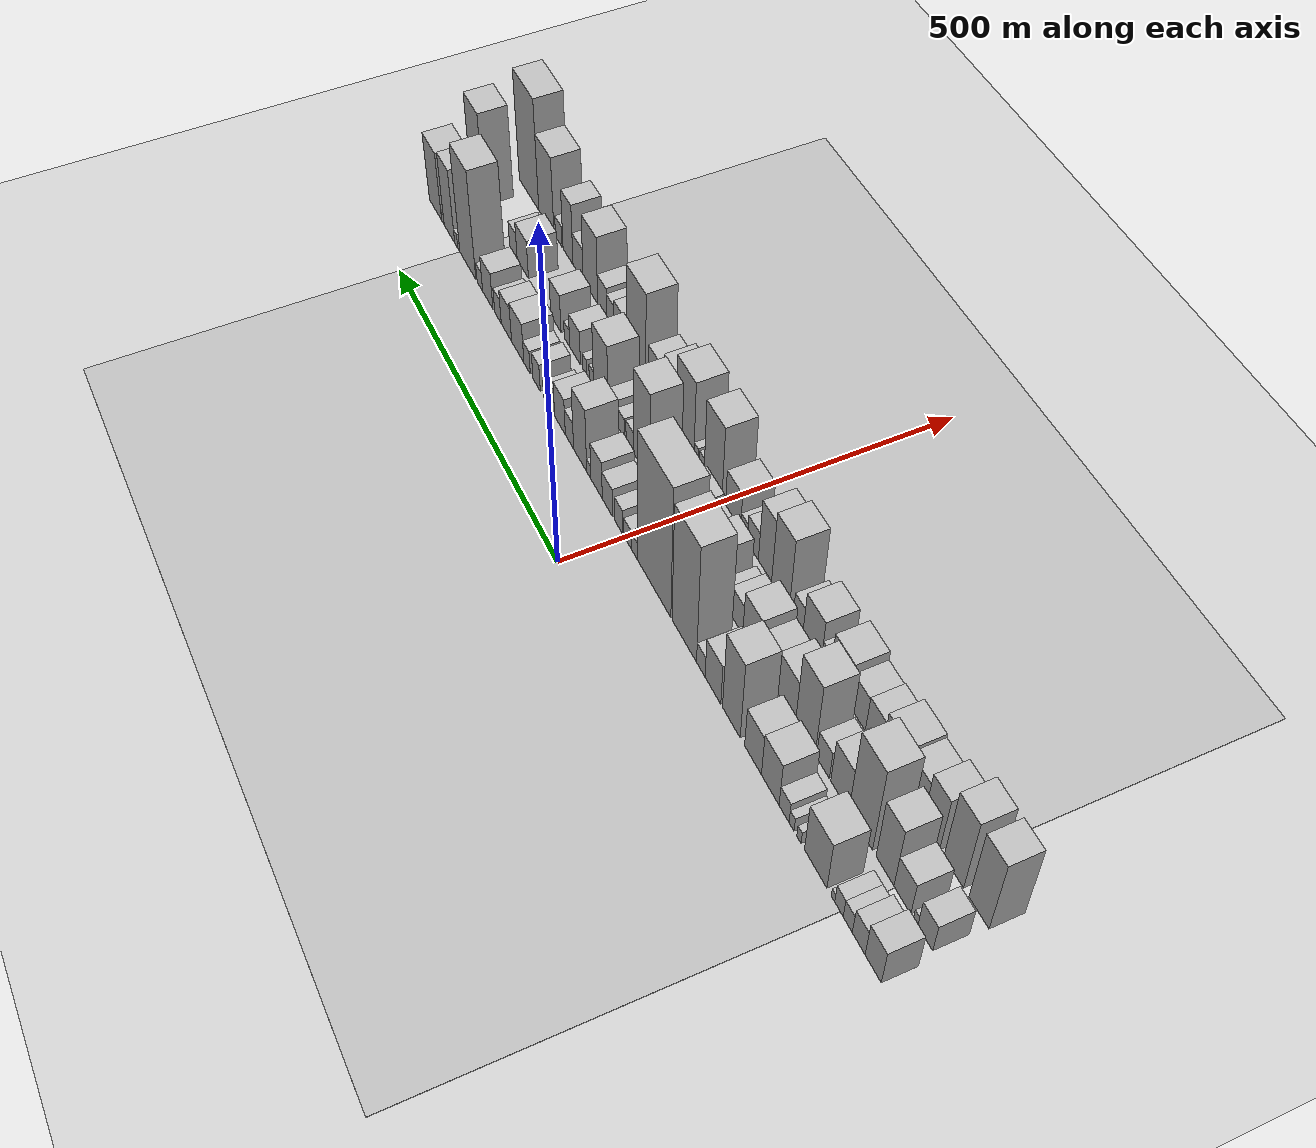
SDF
<?xml version="1.0" encoding="utf-8"?>

<sdf version="1.6">

   <world name="default">

      <gui fullscreen="0">

         <camera name="user_camera">

            <pose>-15 0 4.57585 0 0 0</pose>

            <view_controller>orbit</view_controller>

         </camera>

      </gui>

      <scene>

         <sky>

           <clouds>

             <speed>12</speed>

           </clouds>

         </sky>

         <ambient>0.4 0.4 0.4 1</ambient>

         <background>0.7 0.7 0.7 1</background>

         <shadows>1</shadows>

      </scene>

      <gravity>0 0 -9.8066</gravity>

      <magnetic_field>6e-06 2.3e-05 -4.2e-05</magnetic_field>

      <physics default="0" name="default_physics" type="ode">

         <ode>

            <solver>

               <type>quick</type>

               <iters>10</iters>

               <sor>1.0</sor>

               <use_dynamic_moi_rescaling>0</use_dynamic_moi_rescaling>

            </solver>

            <constraints>

               <cfm>0</cfm>

               <erp>0.2</erp>

               <contact_max_correcting_vel>100</contact_max_correcting_vel>

               <contact_surface_layer>0.001</contact_surface_layer>

            </constraints>

         </ode>

         <max_step_size>0.004</max_step_size>

         <real_time_factor>1</real_time_factor>

         <real_time_update_rate>250</real_time_update_rate>

      </physics>

      <light name="sun" type="directional">

         <cast_shadows>1</cast_shadows>

         <pose>0 0 10 0 0 0</pose>

         <diffuse>0.8 0.8 0.8 1</diffuse>

         <specular>0.2 0.2 0.2 1</specular>

         <attenuation>

            <range>1000</range>

            <constant>0.9</constant>

            <linear>0.01</linear>

            <quadratic>0.001</quadratic>

         </attenuation>

         <direction>-0.5 0.1 -0.9</direction>

      </light>

      <include>

         <name>ground_plane_1</name>

         <uri>model://HANNAS_ground_plane</uri>

         <pose>0 0 0  0 0 0</pose>

      </include>

      <include>

         <name>ground_plane_2</name>

         <uri>model://HANNAS_ground_plane</uri>

         <pose>100 0 0  0 0 0</pose>

      </include>

      <model name="building_1">

         <static>1</static>

         <pose frame="">100.0000 -564.3469 0 0.000000 0.000000 0.000000</pose>

         <link name="link">

            <pose frame="">0 0 30.00 0 0 0</pose>

            <collision name="collision">

               <geometry>

                  <box>

                     <size>40.0000 31.3062 60.0000</size>

                  </box>

               </geometry>

               <max_contacts>10</max_contacts>

               <surface>

                  <contact>

                     <ode/>

                  </contact>

                  <bounce/>

                  <friction>

                     <torsional>

                        <ode/>

                     </torsional>

                     <ode/>

                  </friction>

               </surface>

            </collision>

            <visual name="visual">

               <cast_shadows>0</cast_shadows>

               <geometry>

                  <box>

                     <size>40.0000 31.3062 60.0000</size>

                  </box>

               </geometry>

               <material>

                  <script>

                     <uri>model://HANNAS_wall/materials/scripts</uri>

                     <uri>model://HANNAS_wall/materials/textures</uri>

                     <name>vrc/HANNAS_wall</name>

                  </script>

               </material>

            </visual>

            <self_collide>0</self_collide>

            <enable_wind>0</enable_wind>

            <kinematic>0</kinematic>

         </link>

      </model>

      <model name="building_2">

         <static>1</static>

         <pose frame="">100.0000 -536.2208 0 0.000000 0.000000 0.000000</pose>

         <link name="link">

            <pose frame="">0 0 22.50 0 0 0</pose>

            <collision name="collision">

               <geometry>

                  <box>

                     <size>40.0000 24.9461 45.0000</size>

                  </box>

               </geometry>

               <max_contacts>10</max_contacts>

               <surface>

                  <contact>

                     <ode/>

                  </contact>

                  <bounce/>

                  <friction>

                     <torsional>

                        <ode/>

                     </torsional>

                     <ode/>

                  </friction>

               </surface>

            </collision>

            <visual name="visual">

               <cast_shadows>0</cast_shadows>

               <geometry>

                  <box>

                     <size>40.0000 24.9461 45.0000</size>

                  </box>

               </geometry>

               <material>

                  <script>

                     <uri>model://HANNAS_wall/materials/scripts</uri>

                     <uri>model://HANNAS_wall/materials/textures</uri>

                     <name>vrc/HANNAS_wall</name>

                  </script>

               </material>

            </visual>

            <self_collide>0</self_collide>

            <enable_wind>0</enable_wind>

            <kinematic>0</kinematic>

         </link>

      </model>

      <model name="building_3">

         <static>1</static>

         <pose frame="">100.0000 -514.7291 0 0.000000 0.000000 0.000000</pose>

         <link name="link">

            <pose frame="">0 0 16.50 0 0 0</pose>

            <collision name="collision">

               <geometry>

                  <box>

                     <size>40.0000 18.0373 33.0000</size>

                  </box>

               </geometry>

               <max_contacts>10</max_contacts>

               <surface>

                  <contact>

                     <ode/>

                  </contact>

                  <bounce/>

                  <friction>

                     <torsional>

                        <ode/>

                     </torsional>

                     <ode/>

                  </friction>

               </surface>

            </collision>

            <visual name="visual">

               <cast_shadows>0</cast_shadows>

               <geometry>

                  <box>

                     <size>40.0000 18.0373 33.0000</size>

                  </box>

               </geometry>

               <material>

                  <script>

                     <uri>model://HANNAS_wall/materials/scripts</uri>

                     <uri>model://HANNAS_wall/materials/textures</uri>

                     <name>vrc/HANNAS_wall</name>

                  </script>

               </material>

            </visual>

            <self_collide>0</self_collide>

            <enable_wind>0</enable_wind>

            <kinematic>0</kinematic>

         </link>

      </model>

      <model name="building_4">

         <static>1</static>

         <pose frame="">100.0000 -497.1526 0 0.000000 0.000000 0.000000</pose>

         <link name="link">

            <pose frame="">0 0 16.50 0 0 0</pose>

            <collision name="collision">

               <geometry>

                  <box>

                     <size>40.0000 17.1158 33.0000</size>

                  </box>

               </geometry>

               <max_contacts>10</max_contacts>

               <surface>

                  <contact>

                     <ode/>

                  </contact>

                  <bounce/>

                  <friction>

                     <torsional>

                        <ode/>

                     </torsional>

                     <ode/>

                  </friction>

               </surface>

            </collision>

            <visual name="visual">

               <cast_shadows>0</cast_shadows>

               <geometry>

                  <box>

                     <size>40.0000 17.1158 33.0000</size>

                  </box>

               </geometry>

               <material>

                  <script>

                     <uri>model://HANNAS_wall/materials/scripts</uri>

                     <uri>model://HANNAS_wall/materials/textures</uri>

                     <name>vrc/HANNAS_wall</name>

                  </script>

               </material>

            </visual>

            <self_collide>0</self_collide>

            <enable_wind>0</enable_wind>

            <kinematic>0</kinematic>

         </link>

      </model>

      <model name="building_5">

         <static>1</static>

         <pose frame="">100.0000 -485.1934 0 0.000000 0.000000 0.000000</pose>

         <link name="link">

            <pose frame="">0 0 7.50 0 0 0</pose>

            <collision name="collision">

               <geometry>

                  <box>

                     <size>40.0000 6.8025 15.0000</size>

                  </box>

               </geometry>

               <max_contacts>10</max_contacts>

               <surface>

                  <contact>

                     <ode/>

                  </contact>

                  <bounce/>

                  <friction>

                     <torsional>

                        <ode/>

                     </torsional>

                     <ode/>

                  </friction>

               </surface>

            </collision>

            <visual name="visual">

               <cast_shadows>0</cast_shadows>

               <geometry>

                  <box>

                     <size>40.0000 6.8025 15.0000</size>

                  </box>

               </geometry>

               <material>

                  <script>

                     <uri>model://HANNAS_wall/materials/scripts</uri>

                     <uri>model://HANNAS_wall/materials/textures</uri>

                     <name>vrc/HANNAS_wall</name>

                  </script>

               </material>

            </visual>

            <self_collide>0</self_collide>

            <enable_wind>0</enable_wind>

            <kinematic>0</kinematic>

         </link>

      </model>

      <model name="building_6">

         <static>1</static>

         <pose frame="">100.0000 -449.6014 0 0.000000 0.000000 0.000000</pose>

         <link name="link">

            <pose frame="">0 0 42.00 0 0 0</pose>

            <collision name="collision">

               <geometry>

                  <box>

                     <size>40.0000 46.3815 84.0000</size>

                  </box>

               </geometry>

               <max_contacts>10</max_contacts>

               <surface>

                  <contact>

                     <ode/>

                  </contact>

                  <bounce/>

                  <friction>

                     <torsional>

                        <ode/>

                     </torsional>

                     <ode/>

                  </friction>

               </surface>

            </collision>

            <visual name="visual">

               <cast_shadows>0</cast_shadows>

               <geometry>

                  <box>

                     <size>40.0000 46.3815 84.0000</size>

                  </box>

               </geometry>

               <material>

                  <script>

                     <uri>model://HANNAS_wall/materials/scripts</uri>

                     <uri>model://HANNAS_wall/materials/textures</uri>

                     <name>vrc/HANNAS_wall</name>

                  </script>

               </material>

            </visual>

            <self_collide>0</self_collide>

            <enable_wind>0</enable_wind>

            <kinematic>0</kinematic>

         </link>

      </model>

      <model name="building_7">

         <static>1</static>

         <pose frame="">100.0000 -414.8630 0 0.000000 0.000000 0.000000</pose>

         <link name="link">

            <pose frame="">0 0 10.50 0 0 0</pose>

            <collision name="collision">

               <geometry>

                  <box>

                     <size>40.0000 9.0954 21.0000</size>

                  </box>

               </geometry>

               <max_contacts>10</max_contacts>

               <surface>

                  <contact>

                     <ode/>

                  </contact>

                  <bounce/>

                  <friction>

                     <torsional>

                        <ode/>

                     </torsional>

                     <ode/>

                  </friction>

               </surface>

            </collision>

            <visual name="visual">

               <cast_shadows>0</cast_shadows>

               <geometry>

                  <box>

                     <size>40.0000 9.0954 21.0000</size>

                  </box>

               </geometry>

               <material>

                  <script>

                     <uri>model://HANNAS_wall/materials/scripts</uri>

                     <uri>model://HANNAS_wall/materials/textures</uri>

                     <name>vrc/HANNAS_wall</name>

                  </script>

               </material>

            </visual>

            <self_collide>0</self_collide>

            <enable_wind>0</enable_wind>

            <kinematic>0</kinematic>

         </link>

      </model>

      <model name="building_8">

         <static>1</static>

         <pose frame="">100.0000 -399.0628 0 0.000000 0.000000 0.000000</pose>

         <link name="link">

            <pose frame="">0 0 12.00 0 0 0</pose>

            <collision name="collision">

               <geometry>

                  <box>

                     <size>40.0000 10.5049 24.0000</size>

                  </box>

               </geometry>

               <max_contacts>10</max_contacts>

               <surface>

                  <contact>

                     <ode/>

                  </contact>

                  <bounce/>

                  <friction>

                     <torsional>

                        <ode/>

                     </torsional>

                     <ode/>

                  </friction>

               </surface>

            </collision>

            <visual name="visual">

               <cast_shadows>0</cast_shadows>

               <geometry>

                  <box>

                     <size>40.0000 10.5049 24.0000</size>

                  </box>

               </geometry>

               <material>

                  <script>

                     <uri>model://HANNAS_wall/materials/scripts</uri>

                     <uri>model://HANNAS_wall/materials/textures</uri>

                     <name>vrc/HANNAS_wall</name>

                  </script>

               </material>

            </visual>

            <self_collide>0</self_collide>

            <enable_wind>0</enable_wind>

            <kinematic>0</kinematic>

         </link>

      </model>

      <model name="building_9">

         <static>1</static>

         <pose frame="">100.0000 -383.0492 0 0.000000 0.000000 0.000000</pose>

         <link name="link">

            <pose frame="">0 0 18.00 0 0 0</pose>

            <collision name="collision">

               <geometry>

                  <box>

                     <size>40.0000 21.5223 36.0000</size>

                  </box>

               </geometry>

               <max_contacts>10</max_contacts>

               <surface>

                  <contact>

                     <ode/>

                  </contact>

                  <bounce/>

                  <friction>

                     <torsional>

                        <ode/>

                     </torsional>

                     <ode/>

                  </friction>

               </surface>

            </collision>

            <visual name="visual">

               <cast_shadows>0</cast_shadows>

               <geometry>

                  <box>

                     <size>40.0000 21.5223 36.0000</size>

                  </box>

               </geometry>

               <material>

                  <script>

                     <uri>model://HANNAS_wall/materials/scripts</uri>

                     <uri>model://HANNAS_wall/materials/textures</uri>

                     <name>vrc/HANNAS_wall</name>

                  </script>

               </material>

            </visual>

            <self_collide>0</self_collide>

            <enable_wind>0</enable_wind>

            <kinematic>0</kinematic>

         </link>

      </model>

      <model name="building_10">

         <static>1</static>

         <pose frame="">100.0000 -352.9739 0 0.000000 0.000000 0.000000</pose>

         <link name="link">

            <pose frame="">0 0 37.50 0 0 0</pose>

            <collision name="collision">

               <geometry>

                  <box>

                     <size>40.0000 38.6283 75.0000</size>

                  </box>

               </geometry>

               <max_contacts>10</max_contacts>

               <surface>

                  <contact>

                     <ode/>

                  </contact>

                  <bounce/>

                  <friction>

                     <torsional>

                        <ode/>

                     </torsional>

                     <ode/>

                  </friction>

               </surface>

            </collision>

            <visual name="visual">

               <cast_shadows>0</cast_shadows>

               <geometry>

                  <box>

                     <size>40.0000 38.6283 75.0000</size>

                  </box>

               </geometry>

               <material>

                  <script>

                     <uri>model://HANNAS_wall/materials/scripts</uri>

                     <uri>model://HANNAS_wall/materials/textures</uri>

                     <name>vrc/HANNAS_wall</name>

                  </script>

               </material>

            </visual>

            <self_collide>0</self_collide>

            <enable_wind>0</enable_wind>

            <kinematic>0</kinematic>

         </link>

      </model>

      <model name="building_11">

         <static>1</static>

         <pose frame="">100.0000 -314.8641 0 0.000000 0.000000 0.000000</pose>

         <link name="link">

            <pose frame="">0 0 34.50 0 0 0</pose>

            <collision name="collision">

               <geometry>

                  <box>

                     <size>40.0000 37.5913 69.0000</size>

                  </box>

               </geometry>

               <max_contacts>10</max_contacts>

               <surface>

                  <contact>

                     <ode/>

                  </contact>

                  <bounce/>

                  <friction>

                     <torsional>

                        <ode/>

                     </torsional>

                     <ode/>

                  </friction>

               </surface>

            </collision>

            <visual name="visual">

               <cast_shadows>0</cast_shadows>

               <geometry>

                  <box>

                     <size>40.0000 37.5913 69.0000</size>

                  </box>

               </geometry>

               <material>

                  <script>

                     <uri>model://HANNAS_wall/materials/scripts</uri>

                     <uri>model://HANNAS_wall/materials/textures</uri>

                     <name>vrc/HANNAS_wall</name>

                  </script>

               </material>

            </visual>

            <self_collide>0</self_collide>

            <enable_wind>0</enable_wind>

            <kinematic>0</kinematic>

         </link>

      </model>

      <model name="building_12">

         <static>1</static>

         <pose frame="">100.0000 -265.6356 0 0.000000 0.000000 0.000000</pose>

         <link name="link">

            <pose frame="">0 0 66.00 0 0 0</pose>

            <collision name="collision">

               <geometry>

                  <box>

                     <size>40.0000 40.8657 132.0000</size>

                  </box>

               </geometry>

               <max_contacts>10</max_contacts>

               <surface>

                  <contact>

                     <ode/>

                  </contact>

                  <bounce/>

                  <friction>

                     <torsional>

                        <ode/>

                     </torsional>

                     <ode/>

                  </friction>

               </surface>

            </collision>

            <visual name="visual">

               <cast_shadows>0</cast_shadows>

               <geometry>

                  <box>

                     <size>40.0000 40.8657 132.0000</size>

                  </box>

               </geometry>

               <material>

                  <script>

                     <uri>model://HANNAS_wall/materials/scripts</uri>

                     <uri>model://HANNAS_wall/materials/textures</uri>

                     <name>vrc/HANNAS_wall</name>

                  </script>

               </material>

            </visual>

            <self_collide>0</self_collide>

            <enable_wind>0</enable_wind>

            <kinematic>0</kinematic>

         </link>

      </model>

      <model name="building_13">

         <static>1</static>

         <pose frame="">100.0000 -222.7136 0 0.000000 0.000000 0.000000</pose>

         <link name="link">

            <pose frame="">0 0 34.50 0 0 0</pose>

            <collision name="collision">

               <geometry>

                  <box>

                     <size>40.0000 36.9784 69.0000</size>

                  </box>

               </geometry>

               <max_contacts>10</max_contacts>

               <surface>

                  <contact>

                     <ode/>

                  </contact>

                  <bounce/>

                  <friction>

                     <torsional>

                        <ode/>

                     </torsional>

                     <ode/>

                  </friction>

               </surface>

            </collision>

            <visual name="visual">

               <cast_shadows>0</cast_shadows>

               <geometry>

                  <box>

                     <size>40.0000 36.9784 69.0000</size>

                  </box>

               </geometry>

               <material>

                  <script>

                     <uri>model://HANNAS_wall/materials/scripts</uri>

                     <uri>model://HANNAS_wall/materials/textures</uri>

                     <name>vrc/HANNAS_wall</name>

                  </script>

               </material>

            </visual>

            <self_collide>0</self_collide>

            <enable_wind>0</enable_wind>

            <kinematic>0</kinematic>

         </link>

      </model>

      <model name="building_14">

         <static>1</static>

         <pose frame="">100.0000 -193.8924 0 0.000000 0.000000 0.000000</pose>

         <link name="link">

            <pose frame="">0 0 18.00 0 0 0</pose>

            <collision name="collision">

               <geometry>

                  <box>

                     <size>40.0000 20.6640 36.0000</size>

                  </box>

               </geometry>

               <max_contacts>10</max_contacts>

               <surface>

                  <contact>

                     <ode/>

                  </contact>

                  <bounce/>

                  <friction>

                     <torsional>

                        <ode/>

                     </torsional>

                     <ode/>

                  </friction>

               </surface>

            </collision>

            <visual name="visual">

               <cast_shadows>0</cast_shadows>

               <geometry>

                  <box>

                     <size>40.0000 20.6640 36.0000</size>

                  </box>

               </geometry>

               <material>

                  <script>

                     <uri>model://HANNAS_wall/materials/scripts</uri>

                     <uri>model://HANNAS_wall/materials/textures</uri>

                     <name>vrc/HANNAS_wall</name>

                  </script>

               </material>

            </visual>

            <self_collide>0</self_collide>

            <enable_wind>0</enable_wind>

            <kinematic>0</kinematic>

         </link>

      </model>

      <model name="building_15">

         <static>1</static>

         <pose frame="">100.0000 -153.4347 0 0.000000 0.000000 0.000000</pose>

         <link name="link">

            <pose frame="">0 0 99.00 0 0 0</pose>

            <collision name="collision">

               <geometry>

                  <box>

                     <size>40.0000 60.2513 198.0000</size>

                  </box>

               </geometry>

               <max_contacts>10</max_contacts>

               <surface>

                  <contact>

                     <ode/>

                  </contact>

                  <bounce/>

                  <friction>

                     <torsional>

                        <ode/>

                     </torsional>

                     <ode/>

                  </friction>

               </surface>

            </collision>

            <visual name="visual">

               <cast_shadows>0</cast_shadows>

               <geometry>

                  <box>

                     <size>40.0000 60.2513 198.0000</size>

                  </box>

               </geometry>

               <material>

                  <script>

                     <uri>model://HANNAS_wall/materials/scripts</uri>

                     <uri>model://HANNAS_wall/materials/textures</uri>

                     <name>vrc/HANNAS_wall</name>

                  </script>

               </material>

            </visual>

            <self_collide>0</self_collide>

            <enable_wind>0</enable_wind>

            <kinematic>0</kinematic>

         </link>

      </model>

      <model name="building_16">

         <static>1</static>

         <pose frame="">100.0000 -77.7724 0 0.000000 0.000000 0.000000</pose>

         <link name="link">

            <pose frame="">0 0 109.50 0 0 0</pose>

            <collision name="collision">

               <geometry>

                  <box>

                     <size>40.0000 85.0735 219.0000</size>

                  </box>

               </geometry>

               <max_contacts>10</max_contacts>

               <surface>

                  <contact>

                     <ode/>

                  </contact>

                  <bounce/>

                  <friction>

                     <torsional>

                        <ode/>

                     </torsional>

                     <ode/>

                  </friction>

               </surface>

            </collision>

            <visual name="visual">

               <cast_shadows>0</cast_shadows>

               <geometry>

                  <box>

                     <size>40.0000 85.0735 219.0000</size>

                  </box>

               </geometry>

               <material>

                  <script>

                     <uri>model://HANNAS_wall/materials/scripts</uri>

                     <uri>model://HANNAS_wall/materials/textures</uri>

                     <name>vrc/HANNAS_wall</name>

                  </script>

               </material>

            </visual>

            <self_collide>0</self_collide>

            <enable_wind>0</enable_wind>

            <kinematic>0</kinematic>

         </link>

      </model>

      <model name="building_17">

         <static>1</static>

         <pose frame="">100.0000 -26.6533 0 0.000000 0.000000 0.000000</pose>

         <link name="link">

            <pose frame="">0 0 15.00 0 0 0</pose>

            <collision name="collision">

               <geometry>

                  <box>

                     <size>40.0000 17.1646 30.0000</size>

                  </box>

               </geometry>

               <max_contacts>10</max_contacts>

               <surface>

                  <contact>

                     <ode/>

                  </contact>

                  <bounce/>

                  <friction>

                     <torsional>

                        <ode/>

                     </torsional>

                     <ode/>

                  </friction>

               </surface>

            </collision>

            <visual name="visual">

               <cast_shadows>0</cast_shadows>

               <geometry>

                  <box>

                     <size>40.0000 17.1646 30.0000</size>

                  </box>

               </geometry>

               <material>

                  <script>

                     <uri>model://HANNAS_wall/materials/scripts</uri>

                     <uri>model://HANNAS_wall/materials/textures</uri>

                     <name>vrc/HANNAS_wall</name>

                  </script>

               </material>

            </visual>

            <self_collide>0</self_collide>

            <enable_wind>0</enable_wind>

            <kinematic>0</kinematic>

         </link>

      </model>

      <model name="building_18">

         <static>1</static>

         <pose frame="">100.0000 -8.3352 0 0.000000 0.000000 0.000000</pose>

         <link name="link">

            <pose frame="">0 0 16.50 0 0 0</pose>

            <collision name="collision">

               <geometry>

                  <box>

                     <size>40.0000 19.4717 33.0000</size>

                  </box>

               </geometry>

               <max_contacts>10</max_contacts>

               <surface>

                  <contact>

                     <ode/>

                  </contact>

                  <bounce/>

                  <friction>

                     <torsional>

                        <ode/>

                     </torsional>

                     <ode/>

                  </friction>

               </surface>

            </collision>

            <visual name="visual">

               <cast_shadows>0</cast_shadows>

               <geometry>

                  <box>

                     <size>40.0000 19.4717 33.0000</size>

                  </box>

               </geometry>

               <material>

                  <script>

                     <uri>model://HANNAS_wall/materials/scripts</uri>

                     <uri>model://HANNAS_wall/materials/textures</uri>

                     <name>vrc/HANNAS_wall</name>

                  </script>

               </material>

            </visual>

            <self_collide>0</self_collide>

            <enable_wind>0</enable_wind>

            <kinematic>0</kinematic>

         </link>

      </model>

      <model name="building_19">

         <static>1</static>

         <pose frame="">100.0000 15.1013 0 0.000000 0.000000 0.000000</pose>

         <link name="link">

            <pose frame="">0 0 21.00 0 0 0</pose>

            <collision name="collision">

               <geometry>

                  <box>

                     <size>40.0000 21.4013 42.0000</size>

                  </box>

               </geometry>

               <max_contacts>10</max_contacts>

               <surface>

                  <contact>

                     <ode/>

                  </contact>

                  <bounce/>

                  <friction>

                     <torsional>

                        <ode/>

                     </torsional>

                     <ode/>

                  </friction>

               </surface>

            </collision>

            <visual name="visual">

               <cast_shadows>0</cast_shadows>

               <geometry>

                  <box>

                     <size>40.0000 21.4013 42.0000</size>

                  </box>

               </geometry>

               <material>

                  <script>

                     <uri>model://HANNAS_wall/materials/scripts</uri>

                     <uri>model://HANNAS_wall/materials/textures</uri>

                     <name>vrc/HANNAS_wall</name>

                  </script>

               </material>

            </visual>

            <self_collide>0</self_collide>

            <enable_wind>0</enable_wind>

            <kinematic>0</kinematic>

         </link>

      </model>

      <model name="building_20">

         <static>1</static>

         <pose frame="">100.0000 45.9311 0 0.000000 0.000000 0.000000</pose>

         <link name="link">

            <pose frame="">0 0 24.00 0 0 0</pose>

            <collision name="collision">

               <geometry>

                  <box>

                     <size>40.0000 28.2582 48.0000</size>

                  </box>

               </geometry>

               <max_contacts>10</max_contacts>

               <surface>

                  <contact>

                     <ode/>

                  </contact>

                  <bounce/>

                  <friction>

                     <torsional>

                        <ode/>

                     </torsional>

                     <ode/>

                  </friction>

               </surface>

            </collision>

            <visual name="visual">

               <cast_shadows>0</cast_shadows>

               <geometry>

                  <box>

                     <size>40.0000 28.2582 48.0000</size>

                  </box>

               </geometry>

               <material>

                  <script>

                     <uri>model://HANNAS_wall/materials/scripts</uri>

                     <uri>model://HANNAS_wall/materials/textures</uri>

                     <name>vrc/HANNAS_wall</name>

                  </script>

               </material>

            </visual>

            <self_collide>0</self_collide>

            <enable_wind>0</enable_wind>

            <kinematic>0</kinematic>

         </link>

      </model>

      <model name="building_21">

         <static>1</static>

         <pose frame="">100.0000 75.8250 0 0.000000 0.000000 0.000000</pose>

         <link name="link">

            <pose frame="">0 0 31.50 0 0 0</pose>

            <collision name="collision">

               <geometry>

                  <box>

                     <size>40.0000 31.5296 63.0000</size>

                  </box>

               </geometry>

               <max_contacts>10</max_contacts>

               <surface>

                  <contact>

                     <ode/>

                  </contact>

                  <bounce/>

                  <friction>

                     <torsional>

                        <ode/>

                     </torsional>

                     <ode/>

                  </friction>

               </surface>

            </collision>

            <visual name="visual">

               <cast_shadows>0</cast_shadows>

               <geometry>

                  <box>

                     <size>40.0000 31.5296 63.0000</size>

                  </box>

               </geometry>

               <material>

                  <script>

                     <uri>model://HANNAS_wall/materials/scripts</uri>

                     <uri>model://HANNAS_wall/materials/textures</uri>

                     <name>vrc/HANNAS_wall</name>

                  </script>

               </material>

            </visual>

            <self_collide>0</self_collide>

            <enable_wind>0</enable_wind>

            <kinematic>0</kinematic>

         </link>

      </model>

      <model name="building_22">

         <static>1</static>

         <pose frame="">100.0000 97.4669 0 0.000000 0.000000 0.000000</pose>

         <link name="link">

            <pose frame="">0 0 12.00 0 0 0</pose>

            <collision name="collision">

               <geometry>

                  <box>

                     <size>40.0000 11.7541 24.0000</size>

                  </box>

               </geometry>

               <max_contacts>10</max_contacts>

               <surface>

                  <contact>

                     <ode/>

                  </contact>

                  <bounce/>

                  <friction>

                     <torsional>

                        <ode/>

                     </torsional>

                     <ode/>

                  </friction>

               </surface>

            </collision>

            <visual name="visual">

               <cast_shadows>0</cast_shadows>

               <geometry>

                  <box>

                     <size>40.0000 11.7541 24.0000</size>

                  </box>

               </geometry>

               <material>

                  <script>

                     <uri>model://HANNAS_wall/materials/scripts</uri>

                     <uri>model://HANNAS_wall/materials/textures</uri>

                     <name>vrc/HANNAS_wall</name>

                  </script>

               </material>

            </visual>

            <self_collide>0</self_collide>

            <enable_wind>0</enable_wind>

            <kinematic>0</kinematic>

         </link>

      </model>

      <model name="building_23">

         <static>1</static>

         <pose frame="">100.0000 122.1603 0 0.000000 0.000000 0.000000</pose>

         <link name="link">

            <pose frame="">0 0 52.50 0 0 0</pose>

            <collision name="collision">

               <geometry>

                  <box>

                     <size>40.0000 37.6327 105.0000</size>

                  </box>

               </geometry>

               <max_contacts>10</max_contacts>

               <surface>

                  <contact>

                     <ode/>

                  </contact>

                  <bounce/>

                  <friction>

                     <torsional>

                        <ode/>

                     </torsional>

                     <ode/>

                  </friction>

               </surface>

            </collision>

            <visual name="visual">

               <cast_shadows>0</cast_shadows>

               <geometry>

                  <box>

                     <size>40.0000 37.6327 105.0000</size>

                  </box>

               </geometry>

               <material>

                  <script>

                     <uri>model://HANNAS_wall/materials/scripts</uri>

                     <uri>model://HANNAS_wall/materials/textures</uri>

                     <name>vrc/HANNAS_wall</name>

                  </script>

               </material>

            </visual>

            <self_collide>0</self_collide>

            <enable_wind>0</enable_wind>

            <kinematic>0</kinematic>

         </link>

      </model>

      <model name="building_24">

         <static>1</static>

         <pose frame="">100.0000 152.9874 0 0.000000 0.000000 0.000000</pose>

         <link name="link">

            <pose frame="">0 0 22.50 0 0 0</pose>

            <collision name="collision">

               <geometry>

                  <box>

                     <size>40.0000 24.0217 45.0000</size>

                  </box>

               </geometry>

               <max_contacts>10</max_contacts>

               <surface>

                  <contact>

                     <ode/>

                  </contact>

                  <bounce/>

                  <friction>

                     <torsional>

                        <ode/>

                     </torsional>

                     <ode/>

                  </friction>

               </surface>

            </collision>

            <visual name="visual">

               <cast_shadows>0</cast_shadows>

               <geometry>

                  <box>

                     <size>40.0000 24.0217 45.0000</size>

                  </box>

               </geometry>

               <material>

                  <script>

                     <uri>model://HANNAS_wall/materials/scripts</uri>

                     <uri>model://HANNAS_wall/materials/textures</uri>

                     <name>vrc/HANNAS_wall</name>

                  </script>

               </material>

            </visual>

            <self_collide>0</self_collide>

            <enable_wind>0</enable_wind>

            <kinematic>0</kinematic>

         </link>

      </model>

      <model name="building_25">

         <static>1</static>

         <pose frame="">100.0000 180.6803 0 0.000000 0.000000 0.000000</pose>

         <link name="link">

            <pose frame="">0 0 30.00 0 0 0</pose>

            <collision name="collision">

               <geometry>

                  <box>

                     <size>40.0000 31.3639 60.0000</size>

                  </box>

               </geometry>

               <max_contacts>10</max_contacts>

               <surface>

                  <contact>

                     <ode/>

                  </contact>

                  <bounce/>

                  <friction>

                     <torsional>

                        <ode/>

                     </torsional>

                     <ode/>

                  </friction>

               </surface>

            </collision>

            <visual name="visual">

               <cast_shadows>0</cast_shadows>

               <geometry>

                  <box>

                     <size>40.0000 31.3639 60.0000</size>

                  </box>

               </geometry>

               <material>

                  <script>

                     <uri>model://HANNAS_wall/materials/scripts</uri>

                     <uri>model://HANNAS_wall/materials/textures</uri>

                     <name>vrc/HANNAS_wall</name>

                  </script>

               </material>

            </visual>

            <self_collide>0</self_collide>

            <enable_wind>0</enable_wind>

            <kinematic>0</kinematic>

         </link>

      </model>

      <model name="building_26">

         <static>1</static>

         <pose frame="">100.0000 202.7305 0 0.000000 0.000000 0.000000</pose>

         <link name="link">

            <pose frame="">0 0 13.50 0 0 0</pose>

            <collision name="collision">

               <geometry>

                  <box>

                     <size>40.0000 12.7365 27.0000</size>

                  </box>

               </geometry>

               <max_contacts>10</max_contacts>

               <surface>

                  <contact>

                     <ode/>

                  </contact>

                  <bounce/>

                  <friction>

                     <torsional>

                        <ode/>

                     </torsional>

                     <ode/>

                  </friction>

               </surface>

            </collision>

            <visual name="visual">

               <cast_shadows>0</cast_shadows>

               <geometry>

                  <box>

                     <size>40.0000 12.7365 27.0000</size>

                  </box>

               </geometry>

               <material>

                  <script>

                     <uri>model://HANNAS_wall/materials/scripts</uri>

                     <uri>model://HANNAS_wall/materials/textures</uri>

                     <name>vrc/HANNAS_wall</name>

                  </script>

               </material>

            </visual>

            <self_collide>0</self_collide>

            <enable_wind>0</enable_wind>

            <kinematic>0</kinematic>

         </link>

      </model>

      <model name="building_27">

         <static>1</static>

         <pose frame="">100.0000 221.3108 0 0.000000 0.000000 0.000000</pose>

         <link name="link">

            <pose frame="">0 0 15.00 0 0 0</pose>

            <collision name="collision">

               <geometry>

                  <box>

                     <size>40.0000 16.4240 30.0000</size>

                  </box>

               </geometry>

               <max_contacts>10</max_contacts>

               <surface>

                  <contact>

                     <ode/>

                  </contact>

                  <bounce/>

                  <friction>

                     <torsional>

                        <ode/>

                     </torsional>

                     <ode/>

                  </friction>

               </surface>

            </collision>

            <visual name="visual">

               <cast_shadows>0</cast_shadows>

               <geometry>

                  <box>

                     <size>40.0000 16.4240 30.0000</size>

                  </box>

               </geometry>

               <material>

                  <script>

                     <uri>model://HANNAS_wall/materials/scripts</uri>

                     <uri>model://HANNAS_wall/materials/textures</uri>

                     <name>vrc/HANNAS_wall</name>

                  </script>

               </material>

            </visual>

            <self_collide>0</self_collide>

            <enable_wind>0</enable_wind>

            <kinematic>0</kinematic>

         </link>

      </model>

      <model name="building_28">

         <static>1</static>

         <pose frame="">100.0000 250.7945 0 0.000000 0.000000 0.000000</pose>

         <link name="link">

            <pose frame="">0 0 22.50 0 0 0</pose>

            <collision name="collision">

               <geometry>

                  <box>

                     <size>40.0000 22.5436 45.0000</size>

                  </box>

               </geometry>

               <max_contacts>10</max_contacts>

               <surface>

                  <contact>

                     <ode/>

                  </contact>

                  <bounce/>

                  <friction>

                     <torsional>

                        <ode/>

                     </torsional>

                     <ode/>

                  </friction>

               </surface>

            </collision>

            <visual name="visual">

               <cast_shadows>0</cast_shadows>

               <geometry>

                  <box>

                     <size>40.0000 22.5436 45.0000</size>

                  </box>

               </geometry>

               <material>

                  <script>

                     <uri>model://HANNAS_wall/materials/scripts</uri>

                     <uri>model://HANNAS_wall/materials/textures</uri>

                     <name>vrc/HANNAS_wall</name>

                  </script>

               </material>

            </visual>

            <self_collide>0</self_collide>

            <enable_wind>0</enable_wind>

            <kinematic>0</kinematic>

         </link>

      </model>

      <model name="building_29">

         <static>1</static>

         <pose frame="">100.0000 279.9349 0 0.000000 0.000000 0.000000</pose>

         <link name="link">

            <pose frame="">0 0 19.50 0 0 0</pose>

            <collision name="collision">

               <geometry>

                  <box>

                     <size>40.0000 19.7372 39.0000</size>

                  </box>

               </geometry>

               <max_contacts>10</max_contacts>

               <surface>

                  <contact>

                     <ode/>

                  </contact>

                  <bounce/>

                  <friction>

                     <torsional>

                        <ode/>

                     </torsional>

                     <ode/>

                  </friction>

               </surface>

            </collision>

            <visual name="visual">

               <cast_shadows>0</cast_shadows>

               <geometry>

                  <box>

                     <size>40.0000 19.7372 39.0000</size>

                  </box>

               </geometry>

               <material>

                  <script>

                     <uri>model://HANNAS_wall/materials/scripts</uri>

                     <uri>model://HANNAS_wall/materials/textures</uri>

                     <name>vrc/HANNAS_wall</name>

                  </script>

               </material>

            </visual>

            <self_collide>0</self_collide>

            <enable_wind>0</enable_wind>

            <kinematic>0</kinematic>

         </link>

      </model>

      <model name="building_30">

         <static>1</static>

         <pose frame="">100.0000 309.1752 0 0.000000 0.000000 0.000000</pose>

         <link name="link">

            <pose frame="">0 0 33.00 0 0 0</pose>

            <collision name="collision">

               <geometry>

                  <box>

                     <size>40.0000 38.7434 66.0000</size>

                  </box>

               </geometry>

               <max_contacts>10</max_contacts>

               <surface>

                  <contact>

                     <ode/>

                  </contact>

                  <bounce/>

                  <friction>

                     <torsional>

                        <ode/>

                     </torsional>

                     <ode/>

                  </friction>

               </surface>

            </collision>

            <visual name="visual">

               <cast_shadows>0</cast_shadows>

               <geometry>

                  <box>

                     <size>40.0000 38.7434 66.0000</size>

                  </box>

               </geometry>

               <material>

                  <script>

                     <uri>model://HANNAS_wall/materials/scripts</uri>

                     <uri>model://HANNAS_wall/materials/textures</uri>

                     <name>vrc/HANNAS_wall</name>

                  </script>

               </material>

            </visual>

            <self_collide>0</self_collide>

            <enable_wind>0</enable_wind>

            <kinematic>0</kinematic>

         </link>

      </model>

      <model name="building_31">

         <static>1</static>

         <pose frame="">100.0000 345.0611 0 0.000000 0.000000 0.000000</pose>

         <link name="link">

            <pose frame="">0 0 28.50 0 0 0</pose>

            <collision name="collision">

               <geometry>

                  <box>

                     <size>40.0000 33.0284 57.0000</size>

                  </box>

               </geometry>

               <max_contacts>10</max_contacts>

               <surface>

                  <contact>

                     <ode/>

                  </contact>

                  <bounce/>

                  <friction>

                     <torsional>

                        <ode/>

                     </torsional>

                     <ode/>

                  </friction>

               </surface>

            </collision>

            <visual name="visual">

               <cast_shadows>0</cast_shadows>

               <geometry>

                  <box>

                     <size>40.0000 33.0284 57.0000</size>

                  </box>

               </geometry>

               <material>

                  <script>

                     <uri>model://HANNAS_wall/materials/scripts</uri>

                     <uri>model://HANNAS_wall/materials/textures</uri>

                     <name>vrc/HANNAS_wall</name>

                  </script>

               </material>

            </visual>

            <self_collide>0</self_collide>

            <enable_wind>0</enable_wind>

            <kinematic>0</kinematic>

         </link>

      </model>

      <model name="building_32">

         <static>1</static>

         <pose frame="">100.0000 372.1604 0 0.000000 0.000000 0.000000</pose>

         <link name="link">

            <pose frame="">0 0 21.00 0 0 0</pose>

            <collision name="collision">

               <geometry>

                  <box>

                     <size>40.0000 21.1702 42.0000</size>

                  </box>

               </geometry>

               <max_contacts>10</max_contacts>

               <surface>

                  <contact>

                     <ode/>

                  </contact>

                  <bounce/>

                  <friction>

                     <torsional>

                        <ode/>

                     </torsional>

                     <ode/>

                  </friction>

               </surface>

            </collision>

            <visual name="visual">

               <cast_shadows>0</cast_shadows>

               <geometry>

                  <box>

                     <size>40.0000 21.1702 42.0000</size>

                  </box>

               </geometry>

               <material>

                  <script>

                     <uri>model://HANNAS_wall/materials/scripts</uri>

                     <uri>model://HANNAS_wall/materials/textures</uri>

                     <name>vrc/HANNAS_wall</name>

                  </script>

               </material>

            </visual>

            <self_collide>0</self_collide>

            <enable_wind>0</enable_wind>

            <kinematic>0</kinematic>

         </link>

      </model>

      <model name="building_33">

         <static>1</static>

         <pose frame="">100.0000 405.6801 0 0.000000 0.000000 0.000000</pose>

         <link name="link">

            <pose frame="">0 0 30.00 0 0 0</pose>

            <collision name="collision">

               <geometry>

                  <box>

                     <size>40.0000 33.8693 60.0000</size>

                  </box>

               </geometry>

               <max_contacts>10</max_contacts>

               <surface>

                  <contact>

                     <ode/>

                  </contact>

                  <bounce/>

                  <friction>

                     <torsional>

                        <ode/>

                     </torsional>

                     <ode/>

                  </friction>

               </surface>

            </collision>

            <visual name="visual">

               <cast_shadows>0</cast_shadows>

               <geometry>

                  <box>

                     <size>40.0000 33.8693 60.0000</size>

                  </box>

               </geometry>

               <material>

                  <script>

                     <uri>model://HANNAS_wall/materials/scripts</uri>

                     <uri>model://HANNAS_wall/materials/textures</uri>

                     <name>vrc/HANNAS_wall</name>

                  </script>

               </material>

            </visual>

            <self_collide>0</self_collide>

            <enable_wind>0</enable_wind>

            <kinematic>0</kinematic>

         </link>

      </model>

      <model name="building_34">

         <static>1</static>

         <pose frame="">100.0000 431.8306 0 0.000000 0.000000 0.000000</pose>

         <link name="link">

            <pose frame="">0 0 16.50 0 0 0</pose>

            <collision name="collision">

               <geometry>

                  <box>

                     <size>40.0000 18.4317 33.0000</size>

                  </box>

               </geometry>

               <max_contacts>10</max_contacts>

               <surface>

                  <contact>

                     <ode/>

                  </contact>

                  <bounce/>

                  <friction>

                     <torsional>

                        <ode/>

                     </torsional>

                     <ode/>

                  </friction>

               </surface>

            </collision>

            <visual name="visual">

               <cast_shadows>0</cast_shadows>

               <geometry>

                  <box>

                     <size>40.0000 18.4317 33.0000</size>

                  </box>

               </geometry>

               <material>

                  <script>

                     <uri>model://HANNAS_wall/materials/scripts</uri>

                     <uri>model://HANNAS_wall/materials/textures</uri>

                     <name>vrc/HANNAS_wall</name>

                  </script>

               </material>

            </visual>

            <self_collide>0</self_collide>

            <enable_wind>0</enable_wind>

            <kinematic>0</kinematic>

         </link>

      </model>

      <model name="building_35">

         <static>1</static>

         <pose frame="">100.0000 472.3444 0 0.000000 0.000000 0.000000</pose>

         <link name="link">

            <pose frame="">0 0 88.50 0 0 0</pose>

            <collision name="collision">

               <geometry>

                  <box>

                     <size>40.0000 54.5960 177.0000</size>

                  </box>

               </geometry>

               <max_contacts>10</max_contacts>

               <surface>

                  <contact>

                     <ode/>

                  </contact>

                  <bounce/>

                  <friction>

                     <torsional>

                        <ode/>

                     </torsional>

                     <ode/>

                  </friction>

               </surface>

            </collision>

            <visual name="visual">

               <cast_shadows>0</cast_shadows>

               <geometry>

                  <box>

                     <size>40.0000 54.5960 177.0000</size>

                  </box>

               </geometry>

               <material>

                  <script>

                     <uri>model://HANNAS_wall/materials/scripts</uri>

                     <uri>model://HANNAS_wall/materials/textures</uri>

                     <name>vrc/HANNAS_wall</name>

                  </script>

               </material>

            </visual>

            <self_collide>0</self_collide>

            <enable_wind>0</enable_wind>

            <kinematic>0</kinematic>

         </link>

      </model>

      <model name="building_36">

         <static>1</static>

         <pose frame="">100.0000 503.1276 0 0.000000 0.000000 0.000000</pose>

         <link name="link">

            <pose frame="">0 0 7.50 0 0 0</pose>

            <collision name="collision">

               <geometry>

                  <box>

                     <size>40.0000 6.9704 15.0000</size>

                  </box>

               </geometry>

               <max_contacts>10</max_contacts>

               <surface>

                  <contact>

                     <ode/>

                  </contact>

                  <bounce/>

                  <friction>

                     <torsional>

                        <ode/>

                     </torsional>

                     <ode/>

                  </friction>

               </surface>

            </collision>

            <visual name="visual">

               <cast_shadows>0</cast_shadows>

               <geometry>

                  <box>

                     <size>40.0000 6.9704 15.0000</size>

                  </box>

               </geometry>

               <material>

                  <script>

                     <uri>model://HANNAS_wall/materials/scripts</uri>

                     <uri>model://HANNAS_wall/materials/textures</uri>

                     <name>vrc/HANNAS_wall</name>

                  </script>

               </material>

            </visual>

            <self_collide>0</self_collide>

            <enable_wind>0</enable_wind>

            <kinematic>0</kinematic>

         </link>

      </model>

      <model name="building_37">

         <static>1</static>

         <pose frame="">100.0000 512.1319 0 0.000000 0.000000 0.000000</pose>

         <link name="link">

            <pose frame="">0 0 12.00 0 0 0</pose>

            <collision name="collision">

               <geometry>

                  <box>

                     <size>40.0000 11.0382 24.0000</size>

                  </box>

               </geometry>

               <max_contacts>10</max_contacts>

               <surface>

                  <contact>

                     <ode/>

                  </contact>

                  <bounce/>

                  <friction>

                     <torsional>

                        <ode/>

                     </torsional>

                     <ode/>

                  </friction>

               </surface>

            </collision>

            <visual name="visual">

               <cast_shadows>0</cast_shadows>

               <geometry>

                  <box>

                     <size>40.0000 11.0382 24.0000</size>

                  </box>

               </geometry>

               <material>

                  <script>

                     <uri>model://HANNAS_wall/materials/scripts</uri>

                     <uri>model://HANNAS_wall/materials/textures</uri>

                     <name>vrc/HANNAS_wall</name>

                  </script>

               </material>

            </visual>

            <self_collide>0</self_collide>

            <enable_wind>0</enable_wind>

            <kinematic>0</kinematic>

         </link>

      </model>

      <model name="building_38">

         <static>1</static>

         <pose frame="">100.0000 536.1729 0 0.000000 0.000000 0.000000</pose>

         <link name="link">

            <pose frame="">0 0 60.00 0 0 0</pose>

            <collision name="collision">

               <geometry>

                  <box>

                     <size>40.0000 37.0437 120.0000</size>

                  </box>

               </geometry>

               <max_contacts>10</max_contacts>

               <surface>

                  <contact>

                     <ode/>

                  </contact>

                  <bounce/>

                  <friction>

                     <torsional>

                        <ode/>

                     </torsional>

                     <ode/>

                  </friction>

               </surface>

            </collision>

            <visual name="visual">

               <cast_shadows>0</cast_shadows>

               <geometry>

                  <box>

                     <size>40.0000 37.0437 120.0000</size>

                  </box>

               </geometry>

               <material>

                  <script>

                     <uri>model://HANNAS_wall/materials/scripts</uri>

                     <uri>model://HANNAS_wall/materials/textures</uri>

                     <name>vrc/HANNAS_wall</name>

                  </script>

               </material>

            </visual>

            <self_collide>0</self_collide>

            <enable_wind>0</enable_wind>

            <kinematic>0</kinematic>

         </link>

      </model>

      <model name="building_39">

         <static>1</static>

         <pose frame="">100.0000 559.1173 0 0.000000 0.000000 0.000000</pose>

         <link name="link">

            <pose frame="">0 0 9.00 0 0 0</pose>

            <collision name="collision">

               <geometry>

                  <box>

                     <size>40.0000 8.8453 18.0000</size>

                  </box>

               </geometry>

               <max_contacts>10</max_contacts>

               <surface>

                  <contact>

                     <ode/>

                  </contact>

                  <bounce/>

                  <friction>

                     <torsional>

                        <ode/>

                     </torsional>

                     <ode/>

                  </friction>

               </surface>

            </collision>

            <visual name="visual">

               <cast_shadows>0</cast_shadows>

               <geometry>

                  <box>

                     <size>40.0000 8.8453 18.0000</size>

                  </box>

               </geometry>

               <material>

                  <script>

                     <uri>model://HANNAS_wall/materials/scripts</uri>

                     <uri>model://HANNAS_wall/materials/textures</uri>

                     <name>vrc/HANNAS_wall</name>

                  </script>

               </material>

            </visual>

            <self_collide>0</self_collide>

            <enable_wind>0</enable_wind>

            <kinematic>0</kinematic>

         </link>

      </model>

      <model name="building_40">

         <static>1</static>

         <pose frame="">100.0000 585.4034 0 0.000000 0.000000 0.000000</pose>

         <link name="link">

            <pose frame="">0 0 55.50 0 0 0</pose>

            <collision name="collision">

               <geometry>

                  <box>

                     <size>40.0000 43.7269 111.0000</size>

                  </box>

               </geometry>

               <max_contacts>10</max_contacts>

               <surface>

                  <contact>

                     <ode/>

                  </contact>

                  <bounce/>

                  <friction>

                     <torsional>

                        <ode/>

                     </torsional>

                     <ode/>

                  </friction>

               </surface>

            </collision>

            <visual name="visual">

               <cast_shadows>0</cast_shadows>

               <geometry>

                  <box>

                     <size>40.0000 43.7269 111.0000</size>

                  </box>

               </geometry>

               <material>

                  <script>

                     <uri>model://HANNAS_wall/materials/scripts</uri>

                     <uri>model://HANNAS_wall/materials/textures</uri>

                     <name>vrc/HANNAS_wall</name>

                  </script>

               </material>

            </visual>

            <self_collide>0</self_collide>

            <enable_wind>0</enable_wind>

            <kinematic>0</kinematic>

         </link>

      </model>

      <model name="building_41">

         <static>1</static>

         <pose frame="">160.0000 -557.8670 0 0.000000 0.000000 0.000000</pose>

         <link name="link">

            <pose frame="">0 0 24.00 0 0 0</pose>

            <collision name="collision">

               <geometry>

                  <box>

                     <size>40.0000 28.2659 48.0000</size>

                  </box>

               </geometry>

               <max_contacts>10</max_contacts>

               <surface>

                  <contact>

                     <ode/>

                  </contact>

                  <bounce/>

                  <friction>

                     <torsional>

                        <ode/>

                     </torsional>

                     <ode/>

                  </friction>

               </surface>

            </collision>

            <visual name="visual">

               <cast_shadows>0</cast_shadows>

               <geometry>

                  <box>

                     <size>40.0000 28.2659 48.0000</size>

                  </box>

               </geometry>

               <material>

                  <script>

                     <uri>model://HANNAS_wall/materials/scripts</uri>

                     <uri>model://HANNAS_wall/materials/textures</uri>

                     <name>vrc/HANNAS_wall</name>

                  </script>

               </material>

            </visual>

            <self_collide>0</self_collide>

            <enable_wind>0</enable_wind>

            <kinematic>0</kinematic>

         </link>

      </model>

      <model name="building_42">

         <static>1</static>

         <pose frame="">160.0000 -539.5382 0 0.000000 0.000000 0.000000</pose>

         <link name="link">

            <pose frame="">0 0 9.00 0 0 0</pose>

            <collision name="collision">

               <geometry>

                  <box>

                     <size>40.0000 8.3918 18.0000</size>

                  </box>

               </geometry>

               <max_contacts>10</max_contacts>

               <surface>

                  <contact>

                     <ode/>

                  </contact>

                  <bounce/>

                  <friction>

                     <torsional>

                        <ode/>

                     </torsional>

                     <ode/>

                  </friction>

               </surface>

            </collision>

            <visual name="visual">

               <cast_shadows>0</cast_shadows>

               <geometry>

                  <box>

                     <size>40.0000 8.3918 18.0000</size>

                  </box>

               </geometry>

               <material>

                  <script>

                     <uri>model://HANNAS_wall/materials/scripts</uri>

                     <uri>model://HANNAS_wall/materials/textures</uri>

                     <name>vrc/HANNAS_wall</name>

                  </script>

               </material>

            </visual>

            <self_collide>0</self_collide>

            <enable_wind>0</enable_wind>

            <kinematic>0</kinematic>

         </link>

      </model>

      <model name="building_43">

         <static>1</static>

         <pose frame="">160.0000 -514.0114 0 0.000000 0.000000 0.000000</pose>

         <link name="link">

            <pose frame="">0 0 28.50 0 0 0</pose>

            <collision name="collision">

               <geometry>

                  <box>

                     <size>40.0000 32.6617 57.0000</size>

                  </box>

               </geometry>

               <max_contacts>10</max_contacts>

               <surface>

                  <contact>

                     <ode/>

                  </contact>

                  <bounce/>

                  <friction>

                     <torsional>

                        <ode/>

                     </torsional>

                     <ode/>

                  </friction>

               </surface>

            </collision>

            <visual name="visual">

               <cast_shadows>0</cast_shadows>

               <geometry>

                  <box>

                     <size>40.0000 32.6617 57.0000</size>

                  </box>

               </geometry>

               <material>

                  <script>

                     <uri>model://HANNAS_wall/materials/scripts</uri>

                     <uri>model://HANNAS_wall/materials/textures</uri>

                     <name>vrc/HANNAS_wall</name>

                  </script>

               </material>

            </visual>

            <self_collide>0</self_collide>

            <enable_wind>0</enable_wind>

            <kinematic>0</kinematic>

         </link>

      </model>

      <model name="building_44">

         <static>1</static>

         <pose frame="">160.0000 -479.9670 0 0.000000 0.000000 0.000000</pose>

         <link name="link">

            <pose frame="">0 0 52.50 0 0 0</pose>

            <collision name="collision">

               <geometry>

                  <box>

                     <size>40.0000 35.4271 105.0000</size>

                  </box>

               </geometry>

               <max_contacts>10</max_contacts>

               <surface>

                  <contact>

                     <ode/>

                  </contact>

                  <bounce/>

                  <friction>

                     <torsional>

                        <ode/>

                     </torsional>

                     <ode/>

                  </friction>

               </surface>

            </collision>

            <visual name="visual">

               <cast_shadows>0</cast_shadows>

               <geometry>

                  <box>

                     <size>40.0000 35.4271 105.0000</size>

                  </box>

               </geometry>

               <material>

                  <script>

                     <uri>model://HANNAS_wall/materials/scripts</uri>

                     <uri>model://HANNAS_wall/materials/textures</uri>

                     <name>vrc/HANNAS_wall</name>

                  </script>

               </material>

            </visual>

            <self_collide>0</self_collide>

            <enable_wind>0</enable_wind>

            <kinematic>0</kinematic>

         </link>

      </model>

      <model name="building_45">

         <static>1</static>

         <pose frame="">160.0000 -431.1962 0 0.000000 0.000000 0.000000</pose>

         <link name="link">

            <pose frame="">0 0 73.50 0 0 0</pose>

            <collision name="collision">

               <geometry>

                  <box>

                     <size>40.0000 48.1146 147.0000</size>

                  </box>

               </geometry>

               <max_contacts>10</max_contacts>

               <surface>

                  <contact>

                     <ode/>

                  </contact>

                  <bounce/>

                  <friction>

                     <torsional>

                        <ode/>

                     </torsional>

                     <ode/>

                  </friction>

               </surface>

            </collision>

            <visual name="visual">

               <cast_shadows>0</cast_shadows>

               <geometry>

                  <box>

                     <size>40.0000 48.1146 147.0000</size>

                  </box>

               </geometry>

               <material>

                  <script>

                     <uri>model://HANNAS_wall/materials/scripts</uri>

                     <uri>model://HANNAS_wall/materials/textures</uri>

                     <name>vrc/HANNAS_wall</name>

                  </script>

               </material>

            </visual>

            <self_collide>0</self_collide>

            <enable_wind>0</enable_wind>

            <kinematic>0</kinematic>

         </link>

      </model>

      <model name="building_46">

         <static>1</static>

         <pose frame="">160.0000 -388.1790 0 0.000000 0.000000 0.000000</pose>

         <link name="link">

            <pose frame="">0 0 37.50 0 0 0</pose>

            <collision name="collision">

               <geometry>

                  <box>

                     <size>40.0000 37.9197 75.0000</size>

                  </box>

               </geometry>

               <max_contacts>10</max_contacts>

               <surface>

                  <contact>

                     <ode/>

                  </contact>

                  <bounce/>

                  <friction>

                     <torsional>

                        <ode/>

                     </torsional>

                     <ode/>

                  </friction>

               </surface>

            </collision>

            <visual name="visual">

               <cast_shadows>0</cast_shadows>

               <geometry>

                  <box>

                     <size>40.0000 37.9197 75.0000</size>

                  </box>

               </geometry>

               <material>

                  <script>

                     <uri>model://HANNAS_wall/materials/scripts</uri>

                     <uri>model://HANNAS_wall/materials/textures</uri>

                     <name>vrc/HANNAS_wall</name>

                  </script>

               </material>

            </visual>

            <self_collide>0</self_collide>

            <enable_wind>0</enable_wind>

            <kinematic>0</kinematic>

         </link>

      </model>

      <model name="building_47">

         <static>1</static>

         <pose frame="">160.0000 -352.4566 0 0.000000 0.000000 0.000000</pose>

         <link name="link">

            <pose frame="">0 0 24.00 0 0 0</pose>

            <collision name="collision">

               <geometry>

                  <box>

                     <size>40.0000 27.5251 48.0000</size>

                  </box>

               </geometry>

               <max_contacts>10</max_contacts>

               <surface>

                  <contact>

                     <ode/>

                  </contact>

                  <bounce/>

                  <friction>

                     <torsional>

                        <ode/>

                     </torsional>

                     <ode/>

                  </friction>

               </surface>

            </collision>

            <visual name="visual">

               <cast_shadows>0</cast_shadows>

               <geometry>

                  <box>

                     <size>40.0000 27.5251 48.0000</size>

                  </box>

               </geometry>

               <material>

                  <script>

                     <uri>model://HANNAS_wall/materials/scripts</uri>

                     <uri>model://HANNAS_wall/materials/textures</uri>

                     <name>vrc/HANNAS_wall</name>

                  </script>

               </material>

            </visual>

            <self_collide>0</self_collide>

            <enable_wind>0</enable_wind>

            <kinematic>0</kinematic>

         </link>

      </model>

      <model name="building_48">

         <static>1</static>

         <pose frame="">160.0000 -314.3407 0 0.000000 0.000000 0.000000</pose>

         <link name="link">

            <pose frame="">0 0 61.50 0 0 0</pose>

            <collision name="collision">

               <geometry>

                  <box>

                     <size>40.0000 42.7068 123.0000</size>

                  </box>

               </geometry>

               <max_contacts>10</max_contacts>

               <surface>

                  <contact>

                     <ode/>

                  </contact>

                  <bounce/>

                  <friction>

                     <torsional>

                        <ode/>

                     </torsional>

                     <ode/>

                  </friction>

               </surface>

            </collision>

            <visual name="visual">

               <cast_shadows>0</cast_shadows>

               <geometry>

                  <box>

                     <size>40.0000 42.7068 123.0000</size>

                  </box>

               </geometry>

               <material>

                  <script>

                     <uri>model://HANNAS_wall/materials/scripts</uri>

                     <uri>model://HANNAS_wall/materials/textures</uri>

                     <name>vrc/HANNAS_wall</name>

                  </script>

               </material>

            </visual>

            <self_collide>0</self_collide>

            <enable_wind>0</enable_wind>

            <kinematic>0</kinematic>

         </link>

      </model>

      <model name="building_49">

         <static>1</static>

         <pose frame="">160.0000 -271.8601 0 0.000000 0.000000 0.000000</pose>

         <link name="link">

            <pose frame="">0 0 36.00 0 0 0</pose>

            <collision name="collision">

               <geometry>

                  <box>

                     <size>40.0000 42.2543 72.0000</size>

                  </box>

               </geometry>

               <max_contacts>10</max_contacts>

               <surface>

                  <contact>

                     <ode/>

                  </contact>

                  <bounce/>

                  <friction>

                     <torsional>

                        <ode/>

                     </torsional>

                     <ode/>

                  </friction>

               </surface>

            </collision>

            <visual name="visual">

               <cast_shadows>0</cast_shadows>

               <geometry>

                  <box>

                     <size>40.0000 42.2543 72.0000</size>

                  </box>

               </geometry>

               <material>

                  <script>

                     <uri>model://HANNAS_wall/materials/scripts</uri>

                     <uri>model://HANNAS_wall/materials/textures</uri>

                     <name>vrc/HANNAS_wall</name>

                  </script>

               </material>

            </visual>

            <self_collide>0</self_collide>

            <enable_wind>0</enable_wind>

            <kinematic>0</kinematic>

         </link>

      </model>

      <model name="building_50">

         <static>1</static>

         <pose frame="">160.0000 -228.7493 0 0.000000 0.000000 0.000000</pose>

         <link name="link">

            <pose frame="">0 0 28.50 0 0 0</pose>

            <collision name="collision">

               <geometry>

                  <box>

                     <size>40.0000 33.9673 57.0000</size>

                  </box>

               </geometry>

               <max_contacts>10</max_contacts>

               <surface>

                  <contact>

                     <ode/>

                  </contact>

                  <bounce/>

                  <friction>

                     <torsional>

                        <ode/>

                     </torsional>

                     <ode/>

                  </friction>

               </surface>

            </collision>

            <visual name="visual">

               <cast_shadows>0</cast_shadows>

               <geometry>

                  <box>

                     <size>40.0000 33.9673 57.0000</size>

                  </box>

               </geometry>

               <material>

                  <script>

                     <uri>model://HANNAS_wall/materials/scripts</uri>

                     <uri>model://HANNAS_wall/materials/textures</uri>

                     <name>vrc/HANNAS_wall</name>

                  </script>

               </material>

            </visual>

            <self_collide>0</self_collide>

            <enable_wind>0</enable_wind>

            <kinematic>0</kinematic>

         </link>

      </model>

      <model name="building_51">

         <static>1</static>

         <pose frame="">160.0000 -191.9528 0 0.000000 0.000000 0.000000</pose>

         <link name="link">

            <pose frame="">0 0 37.50 0 0 0</pose>

            <collision name="collision">

               <geometry>

                  <box>

                     <size>40.0000 39.6259 75.0000</size>

                  </box>

               </geometry>

               <max_contacts>10</max_contacts>

               <surface>

                  <contact>

                     <ode/>

                  </contact>

                  <bounce/>

                  <friction>

                     <torsional>

                        <ode/>

                     </torsional>

                     <ode/>

                  </friction>

               </surface>

            </collision>

            <visual name="visual">

               <cast_shadows>0</cast_shadows>

               <geometry>

                  <box>

                     <size>40.0000 39.6259 75.0000</size>

                  </box>

               </geometry>

               <material>

                  <script>

                     <uri>model://HANNAS_wall/materials/scripts</uri>

                     <uri>model://HANNAS_wall/materials/textures</uri>

                     <name>vrc/HANNAS_wall</name>

                  </script>

               </material>

            </visual>

            <self_collide>0</self_collide>

            <enable_wind>0</enable_wind>

            <kinematic>0</kinematic>

         </link>

      </model>

      <model name="building_52">

         <static>1</static>

         <pose frame="">160.0000 -157.3839 0 0.000000 0.000000 0.000000</pose>

         <link name="link">

            <pose frame="">0 0 25.50 0 0 0</pose>

            <collision name="collision">

               <geometry>

                  <box>

                     <size>40.0000 29.5119 51.0000</size>

                  </box>

               </geometry>

               <max_contacts>10</max_contacts>

               <surface>

                  <contact>

                     <ode/>

                  </contact>

                  <bounce/>

                  <friction>

                     <torsional>

                        <ode/>

                     </torsional>

                     <ode/>

                  </friction>

               </surface>

            </collision>

            <visual name="visual">

               <cast_shadows>0</cast_shadows>

               <geometry>

                  <box>

                     <size>40.0000 29.5119 51.0000</size>

                  </box>

               </geometry>

               <material>

                  <script>

                     <uri>model://HANNAS_wall/materials/scripts</uri>

                     <uri>model://HANNAS_wall/materials/textures</uri>

                     <name>vrc/HANNAS_wall</name>

                  </script>

               </material>

            </visual>

            <self_collide>0</self_collide>

            <enable_wind>0</enable_wind>

            <kinematic>0</kinematic>

         </link>

      </model>

      <model name="building_53">

         <static>1</static>

         <pose frame="">160.0000 -132.2535 0 0.000000 0.000000 0.000000</pose>

         <link name="link">

            <pose frame="">0 0 19.50 0 0 0</pose>

            <collision name="collision">

               <geometry>

                  <box>

                     <size>40.0000 20.7489 39.0000</size>

                  </box>

               </geometry>

               <max_contacts>10</max_contacts>

               <surface>

                  <contact>

                     <ode/>

                  </contact>

                  <bounce/>

                  <friction>

                     <torsional>

                        <ode/>

                     </torsional>

                     <ode/>

                  </friction>

               </surface>

            </collision>

            <visual name="visual">

               <cast_shadows>0</cast_shadows>

               <geometry>

                  <box>

                     <size>40.0000 20.7489 39.0000</size>

                  </box>

               </geometry>

               <material>

                  <script>

                     <uri>model://HANNAS_wall/materials/scripts</uri>

                     <uri>model://HANNAS_wall/materials/textures</uri>

                     <name>vrc/HANNAS_wall</name>

                  </script>

               </material>

            </visual>

            <self_collide>0</self_collide>

            <enable_wind>0</enable_wind>

            <kinematic>0</kinematic>

         </link>

      </model>

      <model name="building_54">

         <static>1</static>

         <pose frame="">160.0000 -94.1200 0 0.000000 0.000000 0.000000</pose>

         <link name="link">

            <pose frame="">0 0 37.50 0 0 0</pose>

            <collision name="collision">

               <geometry>

                  <box>

                     <size>40.0000 37.5179 75.0000</size>

                  </box>

               </geometry>

               <max_contacts>10</max_contacts>

               <surface>

                  <contact>

                     <ode/>

                  </contact>

                  <bounce/>

                  <friction>

                     <torsional>

                        <ode/>

                     </torsional>

                     <ode/>

                  </friction>

               </surface>

            </collision>

            <visual name="visual">

               <cast_shadows>0</cast_shadows>

               <geometry>

                  <box>

                     <size>40.0000 37.5179 75.0000</size>

                  </box>

               </geometry>

               <material>

                  <script>

                     <uri>model://HANNAS_wall/materials/scripts</uri>

                     <uri>model://HANNAS_wall/materials/textures</uri>

                     <name>vrc/HANNAS_wall</name>

                  </script>

               </material>

            </visual>

            <self_collide>0</self_collide>

            <enable_wind>0</enable_wind>

            <kinematic>0</kinematic>

         </link>

      </model>

      <model name="building_55">

         <static>1</static>

         <pose frame="">160.0000 -59.0901 0 0.000000 0.000000 0.000000</pose>

         <link name="link">

            <pose frame="">0 0 28.50 0 0 0</pose>

            <collision name="collision">

               <geometry>

                  <box>

                     <size>40.0000 32.5419 57.0000</size>

                  </box>

               </geometry>

               <max_contacts>10</max_contacts>

               <surface>

                  <contact>

                     <ode/>

                  </contact>

                  <bounce/>

                  <friction>

                     <torsional>

                        <ode/>

                     </torsional>

                     <ode/>

                  </friction>

               </surface>

            </collision>

            <visual name="visual">

               <cast_shadows>0</cast_shadows>

               <geometry>

                  <box>

                     <size>40.0000 32.5419 57.0000</size>

                  </box>

               </geometry>

               <material>

                  <script>

                     <uri>model://HANNAS_wall/materials/scripts</uri>

                     <uri>model://HANNAS_wall/materials/textures</uri>

                     <name>vrc/HANNAS_wall</name>

                  </script>

               </material>

            </visual>

            <self_collide>0</self_collide>

            <enable_wind>0</enable_wind>

            <kinematic>0</kinematic>

         </link>

      </model>

      <model name="building_56">

         <static>1</static>

         <pose frame="">160.0000 -21.2460 0 0.000000 0.000000 0.000000</pose>

         <link name="link">

            <pose frame="">0 0 36.00 0 0 0</pose>

            <collision name="collision">

               <geometry>

                  <box>

                     <size>40.0000 43.1464 72.0000</size>

                  </box>

               </geometry>

               <max_contacts>10</max_contacts>

               <surface>

                  <contact>

                     <ode/>

                  </contact>

                  <bounce/>

                  <friction>

                     <torsional>

                        <ode/>

                     </torsional>

                     <ode/>

                  </friction>

               </surface>

            </collision>

            <visual name="visual">

               <cast_shadows>0</cast_shadows>

               <geometry>

                  <box>

                     <size>40.0000 43.1464 72.0000</size>

                  </box>

               </geometry>

               <material>

                  <script>

                     <uri>model://HANNAS_wall/materials/scripts</uri>

                     <uri>model://HANNAS_wall/materials/textures</uri>

                     <name>vrc/HANNAS_wall</name>

                  </script>

               </material>

            </visual>

            <self_collide>0</self_collide>

            <enable_wind>0</enable_wind>

            <kinematic>0</kinematic>

         </link>

      </model>

      <model name="building_57">

         <static>1</static>

         <pose frame="">160.0000 15.5458 0 0.000000 0.000000 0.000000</pose>

         <link name="link">

            <pose frame="">0 0 28.50 0 0 0</pose>

            <collision name="collision">

               <geometry>

                  <box>

                     <size>40.0000 30.4371 57.0000</size>

                  </box>

               </geometry>

               <max_contacts>10</max_contacts>

               <surface>

                  <contact>

                     <ode/>

                  </contact>

                  <bounce/>

                  <friction>

                     <torsional>

                        <ode/>

                     </torsional>

                     <ode/>

                  </friction>

               </surface>

            </collision>

            <visual name="visual">

               <cast_shadows>0</cast_shadows>

               <geometry>

                  <box>

                     <size>40.0000 30.4371 57.0000</size>

                  </box>

               </geometry>

               <material>

                  <script>

                     <uri>model://HANNAS_wall/materials/scripts</uri>

                     <uri>model://HANNAS_wall/materials/textures</uri>

                     <name>vrc/HANNAS_wall</name>

                  </script>

               </material>

            </visual>

            <self_collide>0</self_collide>

            <enable_wind>0</enable_wind>

            <kinematic>0</kinematic>

         </link>

      </model>

      <model name="building_58">

         <static>1</static>

         <pose frame="">160.0000 46.2465 0 0.000000 0.000000 0.000000</pose>

         <link name="link">

            <pose frame="">0 0 21.00 0 0 0</pose>

            <collision name="collision">

               <geometry>

                  <box>

                     <size>40.0000 22.9643 42.0000</size>

                  </box>

               </geometry>

               <max_contacts>10</max_contacts>

               <surface>

                  <contact>

                     <ode/>

                  </contact>

                  <bounce/>

                  <friction>

                     <torsional>

                        <ode/>

                     </torsional>

                     <ode/>

                  </friction>

               </surface>

            </collision>

            <visual name="visual">

               <cast_shadows>0</cast_shadows>

               <geometry>

                  <box>

                     <size>40.0000 22.9643 42.0000</size>

                  </box>

               </geometry>

               <material>

                  <script>

                     <uri>model://HANNAS_wall/materials/scripts</uri>

                     <uri>model://HANNAS_wall/materials/textures</uri>

                     <name>vrc/HANNAS_wall</name>

                  </script>

               </material>

            </visual>

            <self_collide>0</self_collide>

            <enable_wind>0</enable_wind>

            <kinematic>0</kinematic>

         </link>

      </model>

      <model name="building_59">

         <static>1</static>

         <pose frame="">160.0000 84.6311 0 0.000000 0.000000 0.000000</pose>

         <link name="link">

            <pose frame="">0 0 72.00 0 0 0</pose>

            <collision name="collision">

               <geometry>

                  <box>

                     <size>40.0000 43.8050 144.0000</size>

                  </box>

               </geometry>

               <max_contacts>10</max_contacts>

               <surface>

                  <contact>

                     <ode/>

                  </contact>

                  <bounce/>

                  <friction>

                     <torsional>

                        <ode/>

                     </torsional>

                     <ode/>

                  </friction>

               </surface>

            </collision>

            <visual name="visual">

               <cast_shadows>0</cast_shadows>

               <geometry>

                  <box>

                     <size>40.0000 43.8050 144.0000</size>

                  </box>

               </geometry>

               <material>

                  <script>

                     <uri>model://HANNAS_wall/materials/scripts</uri>

                     <uri>model://HANNAS_wall/materials/textures</uri>

                     <name>vrc/HANNAS_wall</name>

                  </script>

               </material>

            </visual>

            <self_collide>0</self_collide>

            <enable_wind>0</enable_wind>

            <kinematic>0</kinematic>

         </link>

      </model>

      <model name="building_60">

         <static>1</static>

         <pose frame="">160.0000 116.9627 0 0.000000 0.000000 0.000000</pose>

         <link name="link">

            <pose frame="">0 0 18.00 0 0 0</pose>

            <collision name="collision">

               <geometry>

                  <box>

                     <size>40.0000 20.8580 36.0000</size>

                  </box>

               </geometry>

               <max_contacts>10</max_contacts>

               <surface>

                  <contact>

                     <ode/>

                  </contact>

                  <bounce/>

                  <friction>

                     <torsional>

                        <ode/>

                     </torsional>

                     <ode/>

                  </friction>

               </surface>

            </collision>

            <visual name="visual">

               <cast_shadows>0</cast_shadows>

               <geometry>

                  <box>

                     <size>40.0000 20.8580 36.0000</size>

                  </box>

               </geometry>

               <material>

                  <script>

                     <uri>model://HANNAS_wall/materials/scripts</uri>

                     <uri>model://HANNAS_wall/materials/textures</uri>

                     <name>vrc/HANNAS_wall</name>

                  </script>

               </material>

            </visual>

            <self_collide>0</self_collide>

            <enable_wind>0</enable_wind>

            <kinematic>0</kinematic>

         </link>

      </model>

      <model name="building_61">

         <static>1</static>

         <pose frame="">160.0000 141.9194 0 0.000000 0.000000 0.000000</pose>

         <link name="link">

            <pose frame="">0 0 16.50 0 0 0</pose>

            <collision name="collision">

               <geometry>

                  <box>

                     <size>40.0000 19.0554 33.0000</size>

                  </box>

               </geometry>

               <max_contacts>10</max_contacts>

               <surface>

                  <contact>

                     <ode/>

                  </contact>

                  <bounce/>

                  <friction>

                     <torsional>

                        <ode/>

                     </torsional>

                     <ode/>

                  </friction>

               </surface>

            </collision>

            <visual name="visual">

               <cast_shadows>0</cast_shadows>

               <geometry>

                  <box>

                     <size>40.0000 19.0554 33.0000</size>

                  </box>

               </geometry>

               <material>

                  <script>

                     <uri>model://HANNAS_wall/materials/scripts</uri>

                     <uri>model://HANNAS_wall/materials/textures</uri>

                     <name>vrc/HANNAS_wall</name>

                  </script>

               </material>

            </visual>

            <self_collide>0</self_collide>

            <enable_wind>0</enable_wind>

            <kinematic>0</kinematic>

         </link>

      </model>

      <model name="building_62">

         <static>1</static>

         <pose frame="">160.0000 162.7937 0 0.000000 0.000000 0.000000</pose>

         <link name="link">

            <pose frame="">0 0 22.50 0 0 0</pose>

            <collision name="collision">

               <geometry>

                  <box>

                     <size>40.0000 22.6934 45.0000</size>

                  </box>

               </geometry>

               <max_contacts>10</max_contacts>

               <surface>

                  <contact>

                     <ode/>

                  </contact>

                  <bounce/>

                  <friction>

                     <torsional>

                        <ode/>

                     </torsional>

                     <ode/>

                  </friction>

               </surface>

            </collision>

            <visual name="visual">

               <cast_shadows>0</cast_shadows>

               <geometry>

                  <box>

                     <size>40.0000 22.6934 45.0000</size>

                  </box>

               </geometry>

               <material>

                  <script>

                     <uri>model://HANNAS_wall/materials/scripts</uri>

                     <uri>model://HANNAS_wall/materials/textures</uri>

                     <name>vrc/HANNAS_wall</name>

                  </script>

               </material>

            </visual>

            <self_collide>0</self_collide>

            <enable_wind>0</enable_wind>

            <kinematic>0</kinematic>

         </link>

      </model>

      <model name="building_63">

         <static>1</static>

         <pose frame="">160.0000 199.1652 0 0.000000 0.000000 0.000000</pose>

         <link name="link">

            <pose frame="">0 0 54.00 0 0 0</pose>

            <collision name="collision">

               <geometry>

                  <box>

                     <size>40.0000 42.0496 108.0000</size>

                  </box>

               </geometry>

               <max_contacts>10</max_contacts>

               <surface>

                  <contact>

                     <ode/>

                  </contact>

                  <bounce/>

                  <friction>

                     <torsional>

                        <ode/>

                     </torsional>

                     <ode/>

                  </friction>

               </surface>

            </collision>

            <visual name="visual">

               <cast_shadows>0</cast_shadows>

               <geometry>

                  <box>

                     <size>40.0000 42.0496 108.0000</size>

                  </box>

               </geometry>

               <material>

                  <script>

                     <uri>model://HANNAS_wall/materials/scripts</uri>

                     <uri>model://HANNAS_wall/materials/textures</uri>

                     <name>vrc/HANNAS_wall</name>

                  </script>

               </material>

            </visual>

            <self_collide>0</self_collide>

            <enable_wind>0</enable_wind>

            <kinematic>0</kinematic>

         </link>

      </model>

      <model name="building_64">

         <static>1</static>

         <pose frame="">160.0000 226.4429 0 0.000000 0.000000 0.000000</pose>

         <link name="link">

            <pose frame="">0 0 13.50 0 0 0</pose>

            <collision name="collision">

               <geometry>

                  <box>

                     <size>40.0000 12.5059 27.0000</size>

                  </box>

               </geometry>

               <max_contacts>10</max_contacts>

               <surface>

                  <contact>

                     <ode/>

                  </contact>

                  <bounce/>

                  <friction>

                     <torsional>

                        <ode/>

                     </torsional>

                     <ode/>

                  </friction>

               </surface>

            </collision>

            <visual name="visual">

               <cast_shadows>0</cast_shadows>

               <geometry>

                  <box>

                     <size>40.0000 12.5059 27.0000</size>

                  </box>

               </geometry>

               <material>

                  <script>

                     <uri>model://HANNAS_wall/materials/scripts</uri>

                     <uri>model://HANNAS_wall/materials/textures</uri>

                     <name>vrc/HANNAS_wall</name>

                  </script>

               </material>

            </visual>

            <self_collide>0</self_collide>

            <enable_wind>0</enable_wind>

            <kinematic>0</kinematic>

         </link>

      </model>

      <model name="building_65">

         <static>1</static>

         <pose frame="">160.0000 246.2078 0 0.000000 0.000000 0.000000</pose>

         <link name="link">

            <pose frame="">0 0 13.50 0 0 0</pose>

            <collision name="collision">

               <geometry>

                  <box>

                     <size>40.0000 13.0239 27.0000</size>

                  </box>

               </geometry>

               <max_contacts>10</max_contacts>

               <surface>

                  <contact>

                     <ode/>

                  </contact>

                  <bounce/>

                  <friction>

                     <torsional>

                        <ode/>

                     </torsional>

                     <ode/>

                  </friction>

               </surface>

            </collision>

            <visual name="visual">

               <cast_shadows>0</cast_shadows>

               <geometry>

                  <box>

                     <size>40.0000 13.0239 27.0000</size>

                  </box>

               </geometry>

               <material>

                  <script>

                     <uri>model://HANNAS_wall/materials/scripts</uri>

                     <uri>model://HANNAS_wall/materials/textures</uri>

                     <name>vrc/HANNAS_wall</name>

                  </script>

               </material>

            </visual>

            <self_collide>0</self_collide>

            <enable_wind>0</enable_wind>

            <kinematic>0</kinematic>

         </link>

      </model>

      <model name="building_66">

         <static>1</static>

         <pose frame="">160.0000 274.7324 0 0.000000 0.000000 0.000000</pose>

         <link name="link">

            <pose frame="">0 0 28.50 0 0 0</pose>

            <collision name="collision">

               <geometry>

                  <box>

                     <size>40.0000 32.0252 57.0000</size>

                  </box>

               </geometry>

               <max_contacts>10</max_contacts>

               <surface>

                  <contact>

                     <ode/>

                  </contact>

                  <bounce/>

                  <friction>

                     <torsional>

                        <ode/>

                     </torsional>

                     <ode/>

                  </friction>

               </surface>

            </collision>

            <visual name="visual">

               <cast_shadows>0</cast_shadows>

               <geometry>

                  <box>

                     <size>40.0000 32.0252 57.0000</size>

                  </box>

               </geometry>

               <material>

                  <script>

                     <uri>model://HANNAS_wall/materials/scripts</uri>

                     <uri>model://HANNAS_wall/materials/textures</uri>

                     <name>vrc/HANNAS_wall</name>

                  </script>

               </material>

            </visual>

            <self_collide>0</self_collide>

            <enable_wind>0</enable_wind>

            <kinematic>0</kinematic>

         </link>

      </model>

      <model name="building_67">

         <static>1</static>

         <pose frame="">160.0000 299.0501 0 0.000000 0.000000 0.000000</pose>

         <link name="link">

            <pose frame="">0 0 15.00 0 0 0</pose>

            <collision name="collision">

               <geometry>

                  <box>

                     <size>40.0000 16.6102 30.0000</size>

                  </box>

               </geometry>

               <max_contacts>10</max_contacts>

               <surface>

                  <contact>

                     <ode/>

                  </contact>

                  <bounce/>

                  <friction>

                     <torsional>

                        <ode/>

                     </torsional>

                     <ode/>

                  </friction>

               </surface>

            </collision>

            <visual name="visual">

               <cast_shadows>0</cast_shadows>

               <geometry>

                  <box>

                     <size>40.0000 16.6102 30.0000</size>

                  </box>

               </geometry>

               <material>

                  <script>

                     <uri>model://HANNAS_wall/materials/scripts</uri>

                     <uri>model://HANNAS_wall/materials/textures</uri>

                     <name>vrc/HANNAS_wall</name>

                  </script>

               </material>

            </visual>

            <self_collide>0</self_collide>

            <enable_wind>0</enable_wind>

            <kinematic>0</kinematic>

         </link>

      </model>

      <model name="building_68">

         <static>1</static>

         <pose frame="">160.0000 333.2027 0 0.000000 0.000000 0.000000</pose>

         <link name="link">

            <pose frame="">0 0 31.50 0 0 0</pose>

            <collision name="collision">

               <geometry>

                  <box>

                     <size>40.0000 31.6950 63.0000</size>

                  </box>

               </geometry>

               <max_contacts>10</max_contacts>

               <surface>

                  <contact>

                     <ode/>

                  </contact>

                  <bounce/>

                  <friction>

                     <torsional>

                        <ode/>

                     </torsional>

                     <ode/>

                  </friction>

               </surface>

            </collision>

            <visual name="visual">

               <cast_shadows>0</cast_shadows>

               <geometry>

                  <box>

                     <size>40.0000 31.6950 63.0000</size>

                  </box>

               </geometry>

               <material>

                  <script>

                     <uri>model://HANNAS_wall/materials/scripts</uri>

                     <uri>model://HANNAS_wall/materials/textures</uri>

                     <name>vrc/HANNAS_wall</name>

                  </script>

               </material>

            </visual>

            <self_collide>0</self_collide>

            <enable_wind>0</enable_wind>

            <kinematic>0</kinematic>

         </link>

      </model>

      <model name="building_69">

         <static>1</static>

         <pose frame="">160.0000 438.1638 0 0.000000 0.000000 0.000000</pose>

         <link name="link">

            <pose frame="">0 0 31.50 0 0 0</pose>

            <collision name="collision">

               <geometry>

                  <box>

                     <size>40.0000 36.7424 63.0000</size>

                  </box>

               </geometry>

               <max_contacts>10</max_contacts>

               <surface>

                  <contact>

                     <ode/>

                  </contact>

                  <bounce/>

                  <friction>

                     <torsional>

                        <ode/>

                     </torsional>

                     <ode/>

                  </friction>

               </surface>

            </collision>

            <visual name="visual">

               <cast_shadows>0</cast_shadows>

               <geometry>

                  <box>

                     <size>40.0000 36.7424 63.0000</size>

                  </box>

               </geometry>

               <material>

                  <script>

                     <uri>model://HANNAS_wall/materials/scripts</uri>

                     <uri>model://HANNAS_wall/materials/textures</uri>

                     <name>vrc/HANNAS_wall</name>

                  </script>

               </material>

            </visual>

            <self_collide>0</self_collide>

            <enable_wind>0</enable_wind>

            <kinematic>0</kinematic>

         </link>

      </model>

      <model name="building_70">

         <static>1</static>

         <pose frame="">160.0000 468.7781 0 0.000000 0.000000 0.000000</pose>

         <link name="link">

            <pose frame="">0 0 22.50 0 0 0</pose>

            <collision name="collision">

               <geometry>

                  <box>

                     <size>40.0000 24.4863 45.0000</size>

                  </box>

               </geometry>

               <max_contacts>10</max_contacts>

               <surface>

                  <contact>

                     <ode/>

                  </contact>

                  <bounce/>

                  <friction>

                     <torsional>

                        <ode/>

                     </torsional>

                     <ode/>

                  </friction>

               </surface>

            </collision>

            <visual name="visual">

               <cast_shadows>0</cast_shadows>

               <geometry>

                  <box>

                     <size>40.0000 24.4863 45.0000</size>

                  </box>

               </geometry>

               <material>

                  <script>

                     <uri>model://HANNAS_wall/materials/scripts</uri>

                     <uri>model://HANNAS_wall/materials/textures</uri>

                     <name>vrc/HANNAS_wall</name>

                  </script>

               </material>

            </visual>

            <self_collide>0</self_collide>

            <enable_wind>0</enable_wind>

            <kinematic>0</kinematic>

         </link>

      </model>

      <model name="building_71">

         <static>1</static>

         <pose frame="">160.0000 589.4472 0 0.000000 0.000000 0.000000</pose>

         <link name="link">

            <pose frame="">0 0 75.00 0 0 0</pose>

            <collision name="collision">

               <geometry>

                  <box>

                     <size>40.0000 46.2839 150.0000</size>

                  </box>

               </geometry>

               <max_contacts>10</max_contacts>

               <surface>

                  <contact>

                     <ode/>

                  </contact>

                  <bounce/>

                  <friction>

                     <torsional>

                        <ode/>

                     </torsional>

                     <ode/>

                  </friction>

               </surface>

            </collision>

            <visual name="visual">

               <cast_shadows>0</cast_shadows>

               <geometry>

                  <box>

                     <size>40.0000 46.2839 150.0000</size>

                  </box>

               </geometry>

               <material>

                  <script>

                     <uri>model://HANNAS_wall/materials/scripts</uri>

                     <uri>model://HANNAS_wall/materials/textures</uri>

                     <name>vrc/HANNAS_wall</name>

                  </script>

               </material>

            </visual>

            <self_collide>0</self_collide>

            <enable_wind>0</enable_wind>

            <kinematic>0</kinematic>

         </link>

      </model>

      <model name="building_72">

         <static>1</static>

         <pose frame="">220.0000 -556.3811 0 0.000000 0.000000 0.000000</pose>

         <link name="link">

            <pose frame="">0 0 61.50 0 0 0</pose>

            <collision name="collision">

               <geometry>

                  <box>

                     <size>40.0000 37.2379 123.0000</size>

                  </box>

               </geometry>

               <max_contacts>10</max_contacts>

               <surface>

                  <contact>

                     <ode/>

                  </contact>

                  <bounce/>

                  <friction>

                     <torsional>

                        <ode/>

                     </torsional>

                     <ode/>

                  </friction>

               </surface>

            </collision>

            <visual name="visual">

               <cast_shadows>0</cast_shadows>

               <geometry>

                  <box>

                     <size>40.0000 37.2379 123.0000</size>

                  </box>

               </geometry>

               <material>

                  <script>

                     <uri>model://HANNAS_wall/materials/scripts</uri>

                     <uri>model://HANNAS_wall/materials/textures</uri>

                     <name>vrc/HANNAS_wall</name>

                  </script>

               </material>

            </visual>

            <self_collide>0</self_collide>

            <enable_wind>0</enable_wind>

            <kinematic>0</kinematic>

         </link>

      </model>

      <model name="building_73">

         <static>1</static>

         <pose frame="">220.0000 -509.0578 0 0.000000 0.000000 0.000000</pose>

         <link name="link">

            <pose frame="">0 0 61.50 0 0 0</pose>

            <collision name="collision">

               <geometry>

                  <box>

                     <size>40.0000 37.4086 123.0000</size>

                  </box>

               </geometry>

               <max_contacts>10</max_contacts>

               <surface>

                  <contact>

                     <ode/>

                  </contact>

                  <bounce/>

                  <friction>

                     <torsional>

                        <ode/>

                     </torsional>

                     <ode/>

                  </friction>

               </surface>

            </collision>

            <visual name="visual">

               <cast_shadows>0</cast_shadows>

               <geometry>

                  <box>

                     <size>40.0000 37.4086 123.0000</size>

                  </box>

               </geometry>

               <material>

                  <script>

                     <uri>model://HANNAS_wall/materials/scripts</uri>

                     <uri>model://HANNAS_wall/materials/textures</uri>

                     <name>vrc/HANNAS_wall</name>

                  </script>

               </material>

            </visual>

            <self_collide>0</self_collide>

            <enable_wind>0</enable_wind>

            <kinematic>0</kinematic>

         </link>

      </model>

      <model name="building_74">

         <static>1</static>

         <pose frame="">220.0000 -465.8394 0 0.000000 0.000000 0.000000</pose>

         <link name="link">

            <pose frame="">0 0 46.50 0 0 0</pose>

            <collision name="collision">

               <geometry>

                  <box>

                     <size>40.0000 33.0282 93.0000</size>

                  </box>

               </geometry>

               <max_contacts>10</max_contacts>

               <surface>

                  <contact>

                     <ode/>

                  </contact>

                  <bounce/>

                  <friction>

                     <torsional>

                        <ode/>

                     </torsional>

                     <ode/>

                  </friction>

               </surface>

            </collision>

            <visual name="visual">

               <cast_shadows>0</cast_shadows>

               <geometry>

                  <box>

                     <size>40.0000 33.0282 93.0000</size>

                  </box>

               </geometry>

               <material>

                  <script>

                     <uri>model://HANNAS_wall/materials/scripts</uri>

                     <uri>model://HANNAS_wall/materials/textures</uri>

                     <name>vrc/HANNAS_wall</name>

                  </script>

               </material>

            </visual>

            <self_collide>0</self_collide>

            <enable_wind>0</enable_wind>

            <kinematic>0</kinematic>

         </link>

      </model>

      <model name="building_75">

         <static>1</static>

         <pose frame="">220.0000 -429.7890 0 0.000000 0.000000 0.000000</pose>

         <link name="link">

            <pose frame="">0 0 37.50 0 0 0</pose>

            <collision name="collision">

               <geometry>

                  <box>

                     <size>40.0000 39.0726 75.0000</size>

                  </box>

               </geometry>

               <max_contacts>10</max_contacts>

               <surface>

                  <contact>

                     <ode/>

                  </contact>

                  <bounce/>

                  <friction>

                     <torsional>

                        <ode/>

                     </torsional>

                     <ode/>

                  </friction>

               </surface>

            </collision>

            <visual name="visual">

               <cast_shadows>0</cast_shadows>

               <geometry>

                  <box>

                     <size>40.0000 39.0726 75.0000</size>

                  </box>

               </geometry>

               <material>

                  <script>

                     <uri>model://HANNAS_wall/materials/scripts</uri>

                     <uri>model://HANNAS_wall/materials/textures</uri>

                     <name>vrc/HANNAS_wall</name>

                  </script>

               </material>

            </visual>

            <self_collide>0</self_collide>

            <enable_wind>0</enable_wind>

            <kinematic>0</kinematic>

         </link>

      </model>

      <model name="building_76">

         <static>1</static>

         <pose frame="">220.0000 -387.8769 0 0.000000 0.000000 0.000000</pose>

         <link name="link">

            <pose frame="">0 0 40.50 0 0 0</pose>

            <collision name="collision">

               <geometry>

                  <box>

                     <size>40.0000 44.7518 81.0000</size>

                  </box>

               </geometry>

               <max_contacts>10</max_contacts>

               <surface>

                  <contact>

                     <ode/>

                  </contact>

                  <bounce/>

                  <friction>

                     <torsional>

                        <ode/>

                     </torsional>

                     <ode/>

                  </friction>

               </surface>

            </collision>

            <visual name="visual">

               <cast_shadows>0</cast_shadows>

               <geometry>

                  <box>

                     <size>40.0000 44.7518 81.0000</size>

                  </box>

               </geometry>

               <material>

                  <script>

                     <uri>model://HANNAS_wall/materials/scripts</uri>

                     <uri>model://HANNAS_wall/materials/textures</uri>

                     <name>vrc/HANNAS_wall</name>

                  </script>

               </material>

            </visual>

            <self_collide>0</self_collide>

            <enable_wind>0</enable_wind>

            <kinematic>0</kinematic>

         </link>

      </model>

      <model name="building_77">

         <static>1</static>

         <pose frame="">220.0000 -348.8510 0 0.000000 0.000000 0.000000</pose>

         <link name="link">

            <pose frame="">0 0 31.50 0 0 0</pose>

            <collision name="collision">

               <geometry>

                  <box>

                     <size>40.0000 33.2999 63.0000</size>

                  </box>

               </geometry>

               <max_contacts>10</max_contacts>

               <surface>

                  <contact>

                     <ode/>

                  </contact>

                  <bounce/>

                  <friction>

                     <torsional>

                        <ode/>

                     </torsional>

                     <ode/>

                  </friction>

               </surface>

            </collision>

            <visual name="visual">

               <cast_shadows>0</cast_shadows>

               <geometry>

                  <box>

                     <size>40.0000 33.2999 63.0000</size>

                  </box>

               </geometry>

               <material>

                  <script>

                     <uri>model://HANNAS_wall/materials/scripts</uri>

                     <uri>model://HANNAS_wall/materials/textures</uri>

                     <name>vrc/HANNAS_wall</name>

                  </script>

               </material>

            </visual>

            <self_collide>0</self_collide>

            <enable_wind>0</enable_wind>

            <kinematic>0</kinematic>

         </link>

      </model>

      <model name="building_78">

         <static>1</static>

         <pose frame="">220.0000 -315.4306 0 0.000000 0.000000 0.000000</pose>

         <link name="link">

            <pose frame="">0 0 30.00 0 0 0</pose>

            <collision name="collision">

               <geometry>

                  <box>

                     <size>40.0000 33.5409 60.0000</size>

                  </box>

               </geometry>

               <max_contacts>10</max_contacts>

               <surface>

                  <contact>

                     <ode/>

                  </contact>

                  <bounce/>

                  <friction>

                     <torsional>

                        <ode/>

                     </torsional>

                     <ode/>

                  </friction>

               </surface>

            </collision>

            <visual name="visual">

               <cast_shadows>0</cast_shadows>

               <geometry>

                  <box>

                     <size>40.0000 33.5409 60.0000</size>

                  </box>

               </geometry>

               <material>

                  <script>

                     <uri>model://HANNAS_wall/materials/scripts</uri>

                     <uri>model://HANNAS_wall/materials/textures</uri>

                     <name>vrc/HANNAS_wall</name>

                  </script>

               </material>

            </visual>

            <self_collide>0</self_collide>

            <enable_wind>0</enable_wind>

            <kinematic>0</kinematic>

         </link>

      </model>

      <model name="building_79">

         <static>1</static>

         <pose frame="">220.0000 -277.4956 0 0.000000 0.000000 0.000000</pose>

         <link name="link">

            <pose frame="">0 0 37.50 0 0 0</pose>

            <collision name="collision">

               <geometry>

                  <box>

                     <size>40.0000 42.3291 75.0000</size>

                  </box>

               </geometry>

               <max_contacts>10</max_contacts>

               <surface>

                  <contact>

                     <ode/>

                  </contact>

                  <bounce/>

                  <friction>

                     <torsional>

                        <ode/>

                     </torsional>

                     <ode/>

                  </friction>

               </surface>

            </collision>

            <visual name="visual">

               <cast_shadows>0</cast_shadows>

               <geometry>

                  <box>

                     <size>40.0000 42.3291 75.0000</size>

                  </box>

               </geometry>

               <material>

                  <script>

                     <uri>model://HANNAS_wall/materials/scripts</uri>

                     <uri>model://HANNAS_wall/materials/textures</uri>

                     <name>vrc/HANNAS_wall</name>

                  </script>

               </material>

            </visual>

            <self_collide>0</self_collide>

            <enable_wind>0</enable_wind>

            <kinematic>0</kinematic>

         </link>

      </model>

      <model name="building_80">

         <static>1</static>

         <pose frame="">220.0000 -246.5379 0 0.000000 0.000000 0.000000</pose>

         <link name="link">

            <pose frame="">0 0 18.00 0 0 0</pose>

            <collision name="collision">

               <geometry>

                  <box>

                     <size>40.0000 19.5864 36.0000</size>

                  </box>

               </geometry>

               <max_contacts>10</max_contacts>

               <surface>

                  <contact>

                     <ode/>

                  </contact>

                  <bounce/>

                  <friction>

                     <torsional>

                        <ode/>

                     </torsional>

                     <ode/>

                  </friction>

               </surface>

            </collision>

            <visual name="visual">

               <cast_shadows>0</cast_shadows>

               <geometry>

                  <box>

                     <size>40.0000 19.5864 36.0000</size>

                  </box>

               </geometry>

               <material>

                  <script>

                     <uri>model://HANNAS_wall/materials/scripts</uri>

                     <uri>model://HANNAS_wall/materials/textures</uri>

                     <name>vrc/HANNAS_wall</name>

                  </script>

               </material>

            </visual>

            <self_collide>0</self_collide>

            <enable_wind>0</enable_wind>

            <kinematic>0</kinematic>

         </link>

      </model>

      <model name="building_81">

         <static>1</static>

         <pose frame="">220.0000 -216.2953 0 0.000000 0.000000 0.000000</pose>

         <link name="link">

            <pose frame="">0 0 34.50 0 0 0</pose>

            <collision name="collision">

               <geometry>

                  <box>

                     <size>40.0000 40.8987 69.0000</size>

                  </box>

               </geometry>

               <max_contacts>10</max_contacts>

               <surface>

                  <contact>

                     <ode/>

                  </contact>

                  <bounce/>

                  <friction>

                     <torsional>

                        <ode/>

                     </torsional>

                     <ode/>

                  </friction>

               </surface>

            </collision>

            <visual name="visual">

               <cast_shadows>0</cast_shadows>

               <geometry>

                  <box>

                     <size>40.0000 40.8987 69.0000</size>

                  </box>

               </geometry>

               <material>

                  <script>

                     <uri>model://HANNAS_wall/materials/scripts</uri>

                     <uri>model://HANNAS_wall/materials/textures</uri>

                     <name>vrc/HANNAS_wall</name>

                  </script>

               </material>

            </visual>

            <self_collide>0</self_collide>

            <enable_wind>0</enable_wind>

            <kinematic>0</kinematic>

         </link>

      </model>

      <model name="building_82">

         <static>1</static>

         <pose frame="">220.0000 -184.4032 0 0.000000 0.000000 0.000000</pose>

         <link name="link">

            <pose frame="">0 0 21.00 0 0 0</pose>

            <collision name="collision">

               <geometry>

                  <box>

                     <size>40.0000 22.8855 42.0000</size>

                  </box>

               </geometry>

               <max_contacts>10</max_contacts>

               <surface>

                  <contact>

                     <ode/>

                  </contact>

                  <bounce/>

                  <friction>

                     <torsional>

                        <ode/>

                     </torsional>

                     <ode/>

                  </friction>

               </surface>

            </collision>

            <visual name="visual">

               <cast_shadows>0</cast_shadows>

               <geometry>

                  <box>

                     <size>40.0000 22.8855 42.0000</size>

                  </box>

               </geometry>

               <material>

                  <script>

                     <uri>model://HANNAS_wall/materials/scripts</uri>

                     <uri>model://HANNAS_wall/materials/textures</uri>

                     <name>vrc/HANNAS_wall</name>

                  </script>

               </material>

            </visual>

            <self_collide>0</self_collide>

            <enable_wind>0</enable_wind>

            <kinematic>0</kinematic>

         </link>

      </model>

      <model name="building_83">

         <static>1</static>

         <pose frame="">220.0000 -143.2648 0 0.000000 0.000000 0.000000</pose>

         <link name="link">

            <pose frame="">0 0 60.00 0 0 0</pose>

            <collision name="collision">

               <geometry>

                  <box>

                     <size>40.0000 41.3913 120.0000</size>

                  </box>

               </geometry>

               <max_contacts>10</max_contacts>

               <surface>

                  <contact>

                     <ode/>

                  </contact>

                  <bounce/>

                  <friction>

                     <torsional>

                        <ode/>

                     </torsional>

                     <ode/>

                  </friction>

               </surface>

            </collision>

            <visual name="visual">

               <cast_shadows>0</cast_shadows>

               <geometry>

                  <box>

                     <size>40.0000 41.3913 120.0000</size>

                  </box>

               </geometry>

               <material>

                  <script>

                     <uri>model://HANNAS_wall/materials/scripts</uri>

                     <uri>model://HANNAS_wall/materials/textures</uri>

                     <name>vrc/HANNAS_wall</name>

                  </script>

               </material>

            </visual>

            <self_collide>0</self_collide>

            <enable_wind>0</enable_wind>

            <kinematic>0</kinematic>

         </link>

      </model>

      <model name="building_84">

         <static>1</static>

         <pose frame="">220.0000 -106.6228 0 0.000000 0.000000 0.000000</pose>

         <link name="link">

            <pose frame="">0 0 52.50 0 0 0</pose>

            <collision name="collision">

               <geometry>

                  <box>

                     <size>40.0000 31.8929 105.0000</size>

                  </box>

               </geometry>

               <max_contacts>10</max_contacts>

               <surface>

                  <contact>

                     <ode/>

                  </contact>

                  <bounce/>

                  <friction>

                     <torsional>

                        <ode/>

                     </torsional>

                     <ode/>

                  </friction>

               </surface>

            </collision>

            <visual name="visual">

               <cast_shadows>0</cast_shadows>

               <geometry>

                  <box>

                     <size>40.0000 31.8929 105.0000</size>

                  </box>

               </geometry>

               <material>

                  <script>

                     <uri>model://HANNAS_wall/materials/scripts</uri>

                     <uri>model://HANNAS_wall/materials/textures</uri>

                     <name>vrc/HANNAS_wall</name>

                  </script>

               </material>

            </visual>

            <self_collide>0</self_collide>

            <enable_wind>0</enable_wind>

            <kinematic>0</kinematic>

         </link>

      </model>

      <model name="building_85">

         <static>1</static>

         <pose frame="">220.0000 -77.1014 0 0.000000 0.000000 0.000000</pose>

         <link name="link">

            <pose frame="">0 0 24.00 0 0 0</pose>

            <collision name="collision">

               <geometry>

                  <box>

                     <size>40.0000 27.1498 48.0000</size>

                  </box>

               </geometry>

               <max_contacts>10</max_contacts>

               <surface>

                  <contact>

                     <ode/>

                  </contact>

                  <bounce/>

                  <friction>

                     <torsional>

                        <ode/>

                     </torsional>

                     <ode/>

                  </friction>

               </surface>

            </collision>

            <visual name="visual">

               <cast_shadows>0</cast_shadows>

               <geometry>

                  <box>

                     <size>40.0000 27.1498 48.0000</size>

                  </box>

               </geometry>

               <material>

                  <script>

                     <uri>model://HANNAS_wall/materials/scripts</uri>

                     <uri>model://HANNAS_wall/materials/textures</uri>

                     <name>vrc/HANNAS_wall</name>

                  </script>

               </material>

            </visual>

            <self_collide>0</self_collide>

            <enable_wind>0</enable_wind>

            <kinematic>0</kinematic>

         </link>

      </model>

      <model name="building_86">

         <static>1</static>

         <pose frame="">220.0000 -55.1406 0 0.000000 0.000000 0.000000</pose>

         <link name="link">

            <pose frame="">0 0 16.50 0 0 0</pose>

            <collision name="collision">

               <geometry>

                  <box>

                     <size>40.0000 16.7718 33.0000</size>

                  </box>

               </geometry>

               <max_contacts>10</max_contacts>

               <surface>

                  <contact>

                     <ode/>

                  </contact>

                  <bounce/>

                  <friction>

                     <torsional>

                        <ode/>

                     </torsional>

                     <ode/>

                  </friction>

               </surface>

            </collision>

            <visual name="visual">

               <cast_shadows>0</cast_shadows>

               <geometry>

                  <box>

                     <size>40.0000 16.7718 33.0000</size>

                  </box>

               </geometry>

               <material>

                  <script>

                     <uri>model://HANNAS_wall/materials/scripts</uri>

                     <uri>model://HANNAS_wall/materials/textures</uri>

                     <name>vrc/HANNAS_wall</name>

                  </script>

               </material>

            </visual>

            <self_collide>0</self_collide>

            <enable_wind>0</enable_wind>

            <kinematic>0</kinematic>

         </link>

      </model>

      <model name="building_87">

         <static>1</static>

         <pose frame="">220.0000 -28.0522 0 0.000000 0.000000 0.000000</pose>

         <link name="link">

            <pose frame="">0 0 33.00 0 0 0</pose>

            <collision name="collision">

               <geometry>

                  <box>

                     <size>40.0000 37.4050 66.0000</size>

                  </box>

               </geometry>

               <max_contacts>10</max_contacts>

               <surface>

                  <contact>

                     <ode/>

                  </contact>

                  <bounce/>

                  <friction>

                     <torsional>

                        <ode/>

                     </torsional>

                     <ode/>

                  </friction>

               </surface>

            </collision>

            <visual name="visual">

               <cast_shadows>0</cast_shadows>

               <geometry>

                  <box>

                     <size>40.0000 37.4050 66.0000</size>

                  </box>

               </geometry>

               <material>

                  <script>

                     <uri>model://HANNAS_wall/materials/scripts</uri>

                     <uri>model://HANNAS_wall/materials/textures</uri>

                     <name>vrc/HANNAS_wall</name>

                  </script>

               </material>

            </visual>

            <self_collide>0</self_collide>

            <enable_wind>0</enable_wind>

            <kinematic>0</kinematic>

         </link>

      </model>

      <model name="building_88">

         <static>1</static>

         <pose frame="">220.0000 22.4431 0 0.000000 0.000000 0.000000</pose>

         <link name="link">

            <pose frame="">0 0 63.00 0 0 0</pose>

            <collision name="collision">

               <geometry>

                  <box>

                     <size>40.0000 45.5857 126.0000</size>

                  </box>

               </geometry>

               <max_contacts>10</max_contacts>

               <surface>

                  <contact>

                     <ode/>

                  </contact>

                  <bounce/>

                  <friction>

                     <torsional>

                        <ode/>

                     </torsional>

                     <ode/>

                  </friction>

               </surface>

            </collision>

            <visual name="visual">

               <cast_shadows>0</cast_shadows>

               <geometry>

                  <box>

                     <size>40.0000 45.5857 126.0000</size>

                  </box>

               </geometry>

               <material>

                  <script>

                     <uri>model://HANNAS_wall/materials/scripts</uri>

                     <uri>model://HANNAS_wall/materials/textures</uri>

                     <name>vrc/HANNAS_wall</name>

                  </script>

               </material>

            </visual>

            <self_collide>0</self_collide>

            <enable_wind>0</enable_wind>

            <kinematic>0</kinematic>

         </link>

      </model>

      <model name="building_89">

         <static>1</static>

         <pose frame="">220.0000 51.6182 0 0.000000 0.000000 0.000000</pose>

         <link name="link">

            <pose frame="">0 0 13.50 0 0 0</pose>

            <collision name="collision">

               <geometry>

                  <box>

                     <size>40.0000 12.7645 27.0000</size>

                  </box>

               </geometry>

               <max_contacts>10</max_contacts>

               <surface>

                  <contact>

                     <ode/>

                  </contact>

                  <bounce/>

                  <friction>

                     <torsional>

                        <ode/>

                     </torsional>

                     <ode/>

                  </friction>

               </surface>

            </collision>

            <visual name="visual">

               <cast_shadows>0</cast_shadows>

               <geometry>

                  <box>

                     <size>40.0000 12.7645 27.0000</size>

                  </box>

               </geometry>

               <material>

                  <script>

                     <uri>model://HANNAS_wall/materials/scripts</uri>

                     <uri>model://HANNAS_wall/materials/textures</uri>

                     <name>vrc/HANNAS_wall</name>

                  </script>

               </material>

            </visual>

            <self_collide>0</self_collide>

            <enable_wind>0</enable_wind>

            <kinematic>0</kinematic>

         </link>

      </model>

      <model name="building_90">

         <static>1</static>

         <pose frame="">220.0000 66.4389 0 0.000000 0.000000 0.000000</pose>

         <link name="link">

            <pose frame="">0 0 13.50 0 0 0</pose>

            <collision name="collision">

               <geometry>

                  <box>

                     <size>40.0000 10.8768 27.0000</size>

                  </box>

               </geometry>

               <max_contacts>10</max_contacts>

               <surface>

                  <contact>

                     <ode/>

                  </contact>

                  <bounce/>

                  <friction>

                     <torsional>

                        <ode/>

                     </torsional>

                     <ode/>

                  </friction>

               </surface>

            </collision>

            <visual name="visual">

               <cast_shadows>0</cast_shadows>

               <geometry>

                  <box>

                     <size>40.0000 10.8768 27.0000</size>

                  </box>

               </geometry>

               <material>

                  <script>

                     <uri>model://HANNAS_wall/materials/scripts</uri>

                     <uri>model://HANNAS_wall/materials/textures</uri>

                     <name>vrc/HANNAS_wall</name>

                  </script>

               </material>

            </visual>

            <self_collide>0</self_collide>

            <enable_wind>0</enable_wind>

            <kinematic>0</kinematic>

         </link>

      </model>

      <model name="building_91">

         <static>1</static>

         <pose frame="">220.0000 95.5271 0 0.000000 0.000000 0.000000</pose>

         <link name="link">

            <pose frame="">0 0 63.00 0 0 0</pose>

            <collision name="collision">

               <geometry>

                  <box>

                     <size>40.0000 47.2995 126.0000</size>

                  </box>

               </geometry>

               <max_contacts>10</max_contacts>

               <surface>

                  <contact>

                     <ode/>

                  </contact>

                  <bounce/>

                  <friction>

                     <torsional>

                        <ode/>

                     </torsional>

                     <ode/>

                  </friction>

               </surface>

            </collision>

            <visual name="visual">

               <cast_shadows>0</cast_shadows>

               <geometry>

                  <box>

                     <size>40.0000 47.2995 126.0000</size>

                  </box>

               </geometry>

               <material>

                  <script>

                     <uri>model://HANNAS_wall/materials/scripts</uri>

                     <uri>model://HANNAS_wall/materials/textures</uri>

                     <name>vrc/HANNAS_wall</name>

                  </script>

               </material>

            </visual>

            <self_collide>0</self_collide>

            <enable_wind>0</enable_wind>

            <kinematic>0</kinematic>

         </link>

      </model>

      <model name="building_92">

         <static>1</static>

         <pose frame="">220.0000 136.6772 0 0.000000 0.000000 0.000000</pose>

         <link name="link">

            <pose frame="">0 0 46.50 0 0 0</pose>

            <collision name="collision">

               <geometry>

                  <box>

                     <size>40.0000 35.0007 93.0000</size>

                  </box>

               </geometry>

               <max_contacts>10</max_contacts>

               <surface>

                  <contact>

                     <ode/>

                  </contact>

                  <bounce/>

                  <friction>

                     <torsional>

                        <ode/>

                     </torsional>

                     <ode/>

                  </friction>

               </surface>

            </collision>

            <visual name="visual">

               <cast_shadows>0</cast_shadows>

               <geometry>

                  <box>

                     <size>40.0000 35.0007 93.0000</size>

                  </box>

               </geometry>

               <material>

                  <script>

                     <uri>model://HANNAS_wall/materials/scripts</uri>

                     <uri>model://HANNAS_wall/materials/textures</uri>

                     <name>vrc/HANNAS_wall</name>

                  </script>

               </material>

            </visual>

            <self_collide>0</self_collide>

            <enable_wind>0</enable_wind>

            <kinematic>0</kinematic>

         </link>

      </model>

      <model name="building_93">

         <static>1</static>

         <pose frame="">220.0000 177.0465 0 0.000000 0.000000 0.000000</pose>

         <link name="link">

            <pose frame="">0 0 34.50 0 0 0</pose>

            <collision name="collision">

               <geometry>

                  <box>

                     <size>40.0000 37.7380 69.0000</size>

                  </box>

               </geometry>

               <max_contacts>10</max_contacts>

               <surface>

                  <contact>

                     <ode/>

                  </contact>

                  <bounce/>

                  <friction>

                     <torsional>

                        <ode/>

                     </torsional>

                     <ode/>

                  </friction>

               </surface>

            </collision>

            <visual name="visual">

               <cast_shadows>0</cast_shadows>

               <geometry>

                  <box>

                     <size>40.0000 37.7380 69.0000</size>

                  </box>

               </geometry>

               <material>

                  <script>

                     <uri>model://HANNAS_wall/materials/scripts</uri>

                     <uri>model://HANNAS_wall/materials/textures</uri>

                     <name>vrc/HANNAS_wall</name>

                  </script>

               </material>

            </visual>

            <self_collide>0</self_collide>

            <enable_wind>0</enable_wind>

            <kinematic>0</kinematic>

         </link>

      </model>

      <model name="building_94">

         <static>1</static>

         <pose frame="">220.0000 230.0142 0 0.000000 0.000000 0.000000</pose>

         <link name="link">

            <pose frame="">0 0 72.00 0 0 0</pose>

            <collision name="collision">

               <geometry>

                  <box>

                     <size>40.0000 54.1974 144.0000</size>

                  </box>

               </geometry>

               <max_contacts>10</max_contacts>

               <surface>

                  <contact>

                     <ode/>

                  </contact>

                  <bounce/>

                  <friction>

                     <torsional>

                        <ode/>

                     </torsional>

                     <ode/>

                  </friction>

               </surface>

            </collision>

            <visual name="visual">

               <cast_shadows>0</cast_shadows>

               <geometry>

                  <box>

                     <size>40.0000 54.1974 144.0000</size>

                  </box>

               </geometry>

               <material>

                  <script>

                     <uri>model://HANNAS_wall/materials/scripts</uri>

                     <uri>model://HANNAS_wall/materials/textures</uri>

                     <name>vrc/HANNAS_wall</name>

                  </script>

               </material>

            </visual>

            <self_collide>0</self_collide>

            <enable_wind>0</enable_wind>

            <kinematic>0</kinematic>

         </link>

      </model>

      <model name="building_95">

         <static>1</static>

         <pose frame="">220.0000 262.0165 0 0.000000 0.000000 0.000000</pose>

         <link name="link">

            <pose frame="">0 0 10.50 0 0 0</pose>

            <collision name="collision">

               <geometry>

                  <box>

                     <size>40.0000 9.8073 21.0000</size>

                  </box>

               </geometry>

               <max_contacts>10</max_contacts>

               <surface>

                  <contact>

                     <ode/>

                  </contact>

                  <bounce/>

                  <friction>

                     <torsional>

                        <ode/>

                     </torsional>

                     <ode/>

                  </friction>

               </surface>

            </collision>

            <visual name="visual">

               <cast_shadows>0</cast_shadows>

               <geometry>

                  <box>

                     <size>40.0000 9.8073 21.0000</size>

                  </box>

               </geometry>

               <material>

                  <script>

                     <uri>model://HANNAS_wall/materials/scripts</uri>

                     <uri>model://HANNAS_wall/materials/textures</uri>

                     <name>vrc/HANNAS_wall</name>

                  </script>

               </material>

            </visual>

            <self_collide>0</self_collide>

            <enable_wind>0</enable_wind>

            <kinematic>0</kinematic>

         </link>

      </model>

      <model name="building_96">

         <static>1</static>

         <pose frame="">220.0000 280.8100 0 0.000000 0.000000 0.000000</pose>

         <link name="link">

            <pose frame="">0 0 25.50 0 0 0</pose>

            <collision name="collision">

               <geometry>

                  <box>

                     <size>40.0000 27.7795 51.0000</size>

                  </box>

               </geometry>

               <max_contacts>10</max_contacts>

               <surface>

                  <contact>

                     <ode/>

                  </contact>

                  <bounce/>

                  <friction>

                     <torsional>

                        <ode/>

                     </torsional>

                     <ode/>

                  </friction>

               </surface>

            </collision>

            <visual name="visual">

               <cast_shadows>0</cast_shadows>

               <geometry>

                  <box>

                     <size>40.0000 27.7795 51.0000</size>

                  </box>

               </geometry>

               <material>

                  <script>

                     <uri>model://HANNAS_wall/materials/scripts</uri>

                     <uri>model://HANNAS_wall/materials/textures</uri>

                     <name>vrc/HANNAS_wall</name>

                  </script>

               </material>

            </visual>

            <self_collide>0</self_collide>

            <enable_wind>0</enable_wind>

            <kinematic>0</kinematic>

         </link>

      </model>

      <model name="building_97">

         <static>1</static>

         <pose frame="">220.0000 305.5985 0 0.000000 0.000000 0.000000</pose>

         <link name="link">

            <pose frame="">0 0 21.00 0 0 0</pose>

            <collision name="collision">

               <geometry>

                  <box>

                     <size>40.0000 21.7974 42.0000</size>

                  </box>

               </geometry>

               <max_contacts>10</max_contacts>

               <surface>

                  <contact>

                     <ode/>

                  </contact>

                  <bounce/>

                  <friction>

                     <torsional>

                        <ode/>

                     </torsional>

                     <ode/>

                  </friction>

               </surface>

            </collision>

            <visual name="visual">

               <cast_shadows>0</cast_shadows>

               <geometry>

                  <box>

                     <size>40.0000 21.7974 42.0000</size>

                  </box>

               </geometry>

               <material>

                  <script>

                     <uri>model://HANNAS_wall/materials/scripts</uri>

                     <uri>model://HANNAS_wall/materials/textures</uri>

                     <name>vrc/HANNAS_wall</name>

                  </script>

               </material>

            </visual>

            <self_collide>0</self_collide>

            <enable_wind>0</enable_wind>

            <kinematic>0</kinematic>

         </link>

      </model>

      <model name="building_98">

         <static>1</static>

         <pose frame="">220.0000 329.9692 0 0.000000 0.000000 0.000000</pose>

         <link name="link">

            <pose frame="">0 0 25.50 0 0 0</pose>

            <collision name="collision">

               <geometry>

                  <box>

                     <size>40.0000 26.9441 51.0000</size>

                  </box>

               </geometry>

               <max_contacts>10</max_contacts>

               <surface>

                  <contact>

                     <ode/>

                  </contact>

                  <bounce/>

                  <friction>

                     <torsional>

                        <ode/>

                     </torsional>

                     <ode/>

                  </friction>

               </surface>

            </collision>

            <visual name="visual">

               <cast_shadows>0</cast_shadows>

               <geometry>

                  <box>

                     <size>40.0000 26.9441 51.0000</size>

                  </box>

               </geometry>

               <material>

                  <script>

                     <uri>model://HANNAS_wall/materials/scripts</uri>

                     <uri>model://HANNAS_wall/materials/textures</uri>

                     <name>vrc/HANNAS_wall</name>

                  </script>

               </material>

            </visual>

            <self_collide>0</self_collide>

            <enable_wind>0</enable_wind>

            <kinematic>0</kinematic>

         </link>

      </model>

      <model name="building_99">

         <static>1</static>

         <pose frame="">220.0000 365.5794 0 0.000000 0.000000 0.000000</pose>

         <link name="link">

            <pose frame="">0 0 55.50 0 0 0</pose>

            <collision name="collision">

               <geometry>

                  <box>

                     <size>40.0000 44.2764 111.0000</size>

                  </box>

               </geometry>

               <max_contacts>10</max_contacts>

               <surface>

                  <contact>

                     <ode/>

                  </contact>

                  <bounce/>

                  <friction>

                     <torsional>

                        <ode/>

                     </torsional>

                     <ode/>

                  </friction>

               </surface>

            </collision>

            <visual name="visual">

               <cast_shadows>0</cast_shadows>

               <geometry>

                  <box>

                     <size>40.0000 44.2764 111.0000</size>

                  </box>

               </geometry>

               <material>

                  <script>

                     <uri>model://HANNAS_wall/materials/scripts</uri>

                     <uri>model://HANNAS_wall/materials/textures</uri>

                     <name>vrc/HANNAS_wall</name>

                  </script>

               </material>

            </visual>

            <self_collide>0</self_collide>

            <enable_wind>0</enable_wind>

            <kinematic>0</kinematic>

         </link>

      </model>

      <model name="building_100">

         <static>1</static>

         <pose frame="">220.0000 403.5796 0 0.000000 0.000000 0.000000</pose>

         <link name="link">

            <pose frame="">0 0 27.00 0 0 0</pose>

            <collision name="collision">

               <geometry>

                  <box>

                     <size>40.0000 31.7239 54.0000</size>

                  </box>

               </geometry>

               <max_contacts>10</max_contacts>

               <surface>

                  <contact>

                     <ode/>

                  </contact>

                  <bounce/>

                  <friction>

                     <torsional>

                        <ode/>

                     </torsional>

                     <ode/>

                  </friction>

               </surface>

            </collision>

            <visual name="visual">

               <cast_shadows>0</cast_shadows>

               <geometry>

                  <box>

                     <size>40.0000 31.7239 54.0000</size>

                  </box>

               </geometry>

               <material>

                  <script>

                     <uri>model://HANNAS_wall/materials/scripts</uri>

                     <uri>model://HANNAS_wall/materials/textures</uri>

                     <name>vrc/HANNAS_wall</name>

                  </script>

               </material>

            </visual>

            <self_collide>0</self_collide>

            <enable_wind>0</enable_wind>

            <kinematic>0</kinematic>

         </link>

      </model>

      <model name="building_101">

         <static>1</static>

         <pose frame="">220.0000 435.1338 0 0.000000 0.000000 0.000000</pose>

         <link name="link">

            <pose frame="">0 0 49.50 0 0 0</pose>

            <collision name="collision">

               <geometry>

                  <box>

                     <size>40.0000 31.3846 99.0000</size>

                  </box>

               </geometry>

               <max_contacts>10</max_contacts>

               <surface>

                  <contact>

                     <ode/>

                  </contact>

                  <bounce/>

                  <friction>

                     <torsional>

                        <ode/>

                     </torsional>

                     <ode/>

                  </friction>

               </surface>

            </collision>

            <visual name="visual">

               <cast_shadows>0</cast_shadows>

               <geometry>

                  <box>

                     <size>40.0000 31.3846 99.0000</size>

                  </box>

               </geometry>

               <material>

                  <script>

                     <uri>model://HANNAS_wall/materials/scripts</uri>

                     <uri>model://HANNAS_wall/materials/textures</uri>

                     <name>vrc/HANNAS_wall</name>

                  </script>

               </material>

            </visual>

            <self_collide>0</self_collide>

            <enable_wind>0</enable_wind>

            <kinematic>0</kinematic>

         </link>

      </model>

      <model name="building_102">

         <static>1</static>

         <pose frame="">220.0000 464.3476 0 0.000000 0.000000 0.000000</pose>

         <link name="link">

            <pose frame="">0 0 18.00 0 0 0</pose>

            <collision name="collision">

               <geometry>

                  <box>

                     <size>40.0000 21.0430 36.0000</size>

                  </box>

               </geometry>

               <max_contacts>10</max_contacts>

               <surface>

                  <contact>

                     <ode/>

                  </contact>

                  <bounce/>

                  <friction>

                     <torsional>

                        <ode/>

                     </torsional>

                     <ode/>

                  </friction>

               </surface>

            </collision>

            <visual name="visual">

               <cast_shadows>0</cast_shadows>

               <geometry>

                  <box>

                     <size>40.0000 21.0430 36.0000</size>

                  </box>

               </geometry>

               <material>

                  <script>

                     <uri>model://HANNAS_wall/materials/scripts</uri>

                     <uri>model://HANNAS_wall/materials/textures</uri>

                     <name>vrc/HANNAS_wall</name>

                  </script>

               </material>

            </visual>

            <self_collide>0</self_collide>

            <enable_wind>0</enable_wind>

            <kinematic>0</kinematic>

         </link>

      </model>

      <model name="building_103">

         <static>1</static>

         <pose frame="">220.0000 504.6382 0 0.000000 0.000000 0.000000</pose>

         <link name="link">

            <pose frame="">0 0 63.00 0 0 0</pose>

            <collision name="collision">

               <geometry>

                  <box>

                     <size>40.0000 49.5382 126.0000</size>

                  </box>

               </geometry>

               <max_contacts>10</max_contacts>

               <surface>

                  <contact>

                     <ode/>

                  </contact>

                  <bounce/>

                  <friction>

                     <torsional>

                        <ode/>

                     </torsional>

                     <ode/>

                  </friction>

               </surface>

            </collision>

            <visual name="visual">

               <cast_shadows>0</cast_shadows>

               <geometry>

                  <box>

                     <size>40.0000 49.5382 126.0000</size>

                  </box>

               </geometry>

               <material>

                  <script>

                     <uri>model://HANNAS_wall/materials/scripts</uri>

                     <uri>model://HANNAS_wall/materials/textures</uri>

                     <name>vrc/HANNAS_wall</name>

                  </script>

               </material>

            </visual>

            <self_collide>0</self_collide>

            <enable_wind>0</enable_wind>

            <kinematic>0</kinematic>

         </link>

      </model>

      <model name="building_104">

         <static>1</static>

         <pose frame="">220.0000 561.9141 0 0.000000 0.000000 0.000000</pose>

         <link name="link">

            <pose frame="">0 0 90.00 0 0 0</pose>

            <collision name="collision">

               <geometry>

                  <box>

                     <size>40.0000 65.0137 180.0000</size>

                  </box>

               </geometry>

               <max_contacts>10</max_contacts>

               <surface>

                  <contact>

                     <ode/>

                  </contact>

                  <bounce/>

                  <friction>

                     <torsional>

                        <ode/>

                     </torsional>

                     <ode/>

                  </friction>

               </surface>

            </collision>

            <visual name="visual">

               <cast_shadows>0</cast_shadows>

               <geometry>

                  <box>

                     <size>40.0000 65.0137 180.0000</size>

                  </box>

               </geometry>

               <material>

                  <script>

                     <uri>model://HANNAS_wall/materials/scripts</uri>

                     <uri>model://HANNAS_wall/materials/textures</uri>

                     <name>vrc/HANNAS_wall</name>

                  </script>

               </material>

            </visual>

            <self_collide>0</self_collide>

            <enable_wind>0</enable_wind>

            <kinematic>0</kinematic>

         </link>

      </model>

   </world>

</sdf>

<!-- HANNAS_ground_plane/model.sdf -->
<sdf version="1.4">
<model name="HANNAS_ground_plane">
  <static>true</static>
    <link name="link">
      <collision name="collision">
        <geometry>
          <plane>
            <normal>0 0 1</normal>
            <size>1000 1000</size>
          </plane>
        </geometry>
        <surface>
          <friction>
            <ode>
              <mu>100</mu>
              <mu2>50</mu2>
            </ode>
          </friction>
        </surface>
      </collision>
      <visual name="visual">
        <cast_shadows>false</cast_shadows>
        <geometry>
          <plane>
            <normal>0 0 1</normal>
            <size>1000 1000</size>
          </plane>
        </geometry>
        <material>
          <script>
            <uri>model://HANNAS_ground_plane/materials/scripts/HANNAS_ground_plane.material</uri>
	    <uri>model://HANNAS_ground_plane/materials/textures</uri>
            <name>HANNASGroundPlane/Image</name>
          </script>
        </material>
      </visual>
    </link>
  </model>
</sdf>
